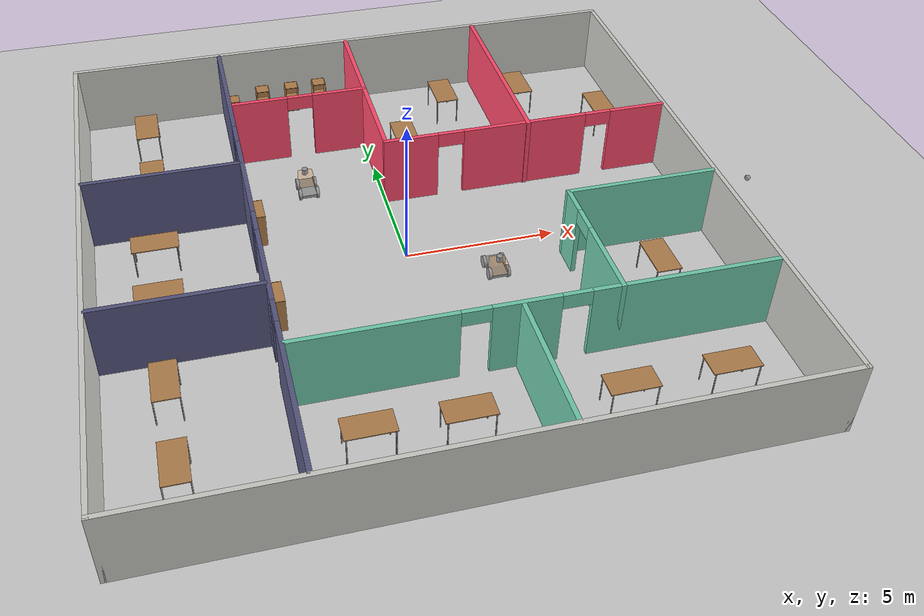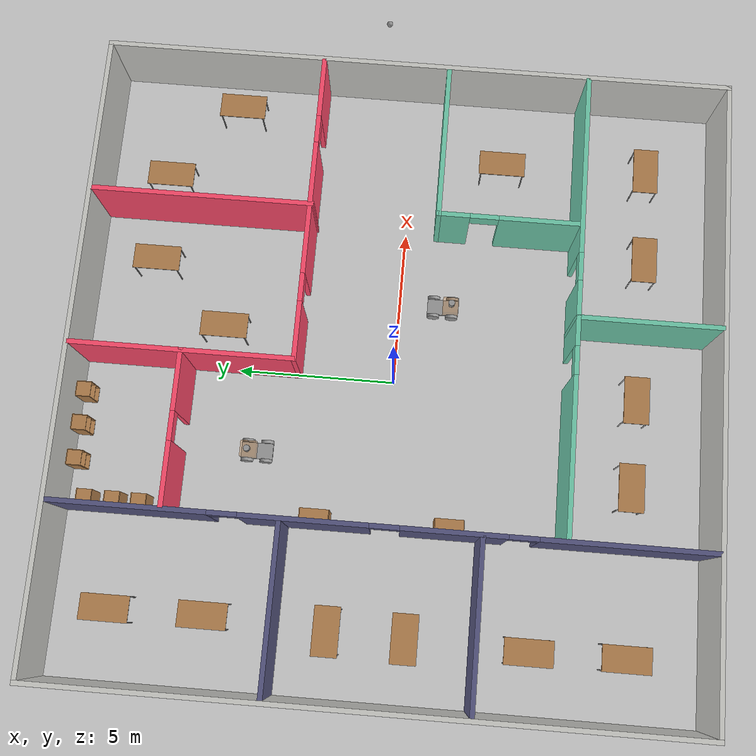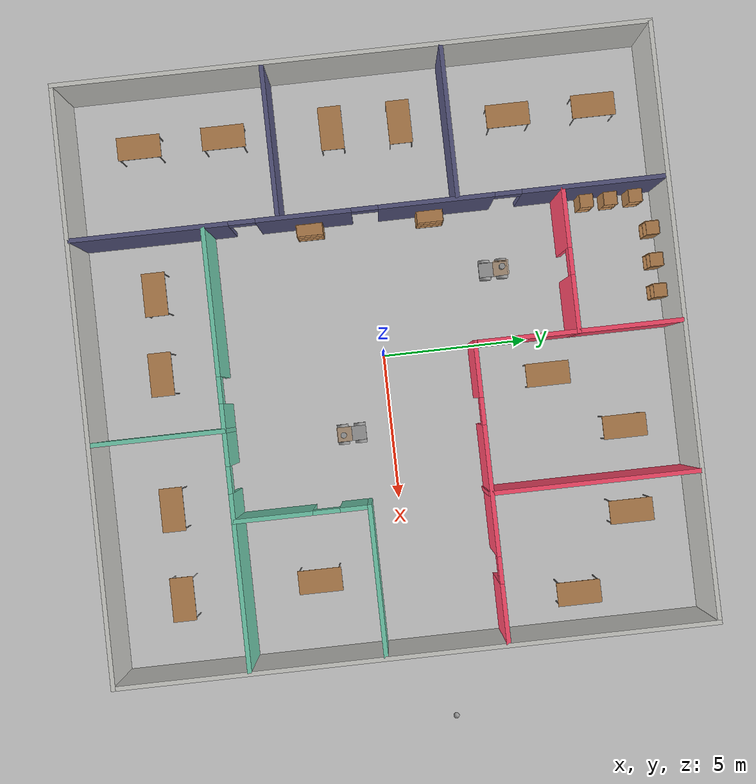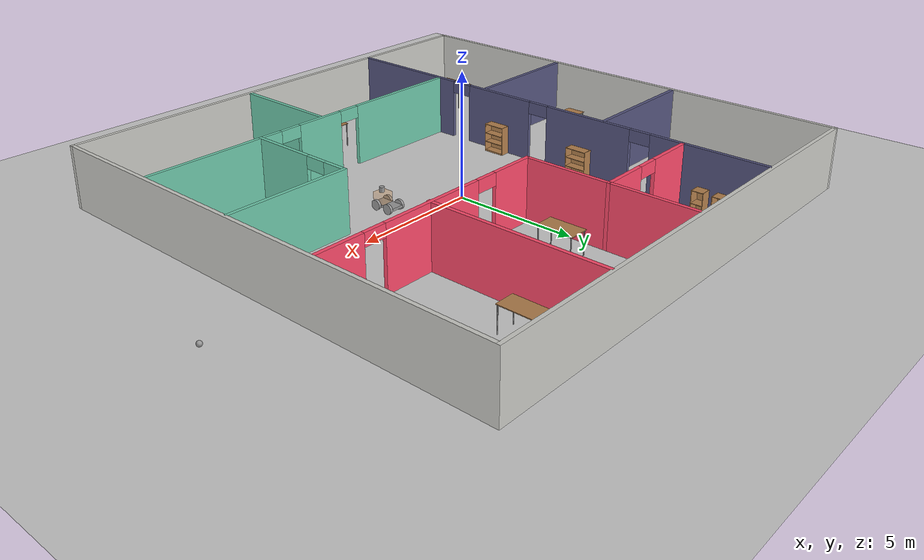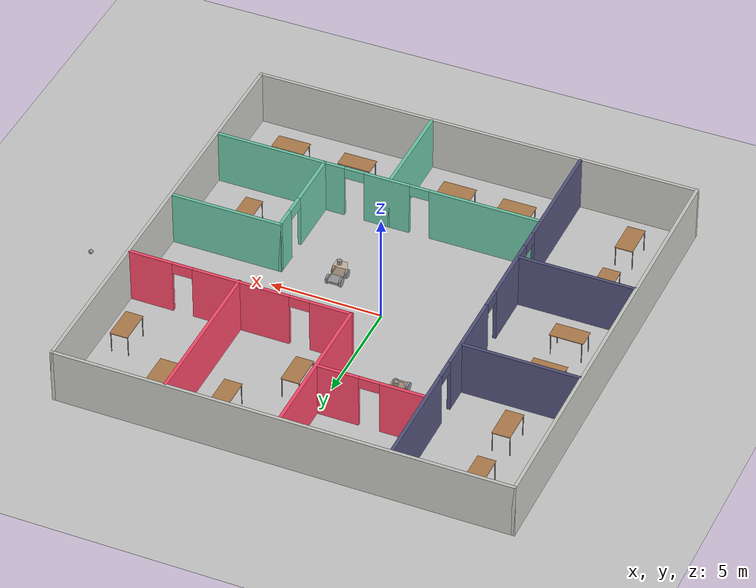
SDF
<sdf version="1.6">
 <world name="default">
  <plugin name="welcome_message" filename="libwelcome_message.so"/>
  <light name="sun" type="directional">
   <pose>0 0 10 0 -0 0</pose>
   <diffuse>0.8 0.8 0.8 1</diffuse>
   <specular>0.2 0.2 0.2 1</specular>
   <attenuation>
    <range>1000</range>
    <constant>0.9</constant>
    <linear>0.01</linear>
    <quadratic>0.001</quadratic>
   </attenuation>
   <direction>-0.5 0.1 -0.9</direction>
  </light>
  <model name="ground_plane">
   <static>1</static>
   <link name="link">
    <collision name="collision">
     <geometry><plane><normal>0 0 1</normal><size>100 100</size></plane></geometry>
     <surface>
      <contact><collide_bitmask>65535</collide_bitmask></contact>
      <friction><ode><mu>100</mu><mu2>50</mu2></ode></friction>
     </surface>
    </collision>
    <visual name="visual">
     <cast_shadows>0</cast_shadows>
     <geometry><plane><normal>0 0 1</normal><size>100 100</size></plane></geometry>
     <material>
      <script><uri>file://media/materials/scripts/gazebo.material</uri><name>Gazebo/Grey</name></script>
     </material>
    </visual>
   </link>
  </model>
  <gravity>0 0 -9.8</gravity>
  <magnetic_field>6e-06 2.3e-05 -4.2e-05</magnetic_field>
  <atmosphere type="adiabatic"/>
  <physics name="default_physics" default="0" type="ode">
   <max_step_size>0.001</max_step_size>
   <real_time_factor>1</real_time_factor>
   <real_time_update_rate>1000</real_time_update_rate>
  </physics>
  <scene><ambient>0.4 0.4 0.4 1</ambient><background>0.7 0.7 0.7 1</background><shadows>1</shadows></scene>
  <spherical_coordinates>
   <surface_model>EARTH_WGS84</surface_model>
   <latitude_deg>0</latitude_deg>
   <longitude_deg>0</longitude_deg>
   <elevation>0</elevation>
   <heading_deg>0</heading_deg>
  </spherical_coordinates>
  <model name="building">
   <link name="Wall_0">
    <collision name="Wall_0_Collision">
     <geometry><box><size>20.15 0.15 2.5</size></box></geometry>
     <pose>0 0 1.25 0 -0 0</pose>
    </collision>
    <visual name="Wall_0_Visual">
     <pose>0 0 1.25 0 -0 0</pose>
     <geometry><box><size>20.15 0.15 2.5</size></box></geometry>
     <material>
      <script><uri>file://media/materials/scripts/gazebo.material</uri><name>Gazebo/CeilingTiled</name></script>
      <ambient>1 1 1 1</ambient>
     </material>
     <meta><layer>0</layer></meta>
    </visual>
    <pose>0 -10 0 0 -0 0</pose>
   </link>
   <link name="Wall_11">
    <collision name="Wall_11_Collision">
     <geometry><box><size>4.55 0.15 2.5</size></box></geometry>
     <pose>0 0 1.25 0 -0 0</pose>
    </collision>
    <visual name="Wall_11_Visual">
     <pose>0 0 1.25 0 -0 0</pose>
     <geometry><box><size>4.55 0.15 2.5</size></box></geometry>
     <material>
      <script><uri>file://media/materials/scripts/gazebo.material</uri><name>Gazebo/Grey</name></script>
      <ambient>0.435294 0.796078 0.67451 1</ambient>
     </material>
     <meta><layer>0</layer></meta>
    </visual>
    <pose>2 -7.7 0 0 0 -1.5708</pose>
   </link>
   <link name="Wall_13">
    <pose>-2.35 6.5 0 0 -0 0</pose>
    <visual name="Wall_13_Visual_0">
     <pose>-1.42755 0 1.25 0 -0 0</pose>
     <geometry><box><size>1.99489 0.15 2.5</size></box></geometry>
     <material>
      <script><uri>file://media/materials/scripts/gazebo.material</uri><name>Gazebo/Grey</name></script>
      <ambient>1 0.290196 0.419608 1</ambient>
     </material>
     <meta><layer>0</layer></meta>
    </visual>
    <collision name="Wall_13_Collision_0">
     <geometry><box><size>1.99489 0.15 2.5</size></box></geometry>
     <pose>-1.42755 0 1.25 0 -0 0</pose>
    </collision>
    <visual name="Wall_13_Visual_1">
     <pose>1.44745 0 1.25 0 -0 0</pose>
     <geometry><box><size>1.95511 0.15 2.5</size></box></geometry>
     <material>
      <script><uri>file://media/materials/scripts/gazebo.material</uri><name>Gazebo/Grey</name></script>
      <ambient>1 0.290196 0.419608 1</ambient>
     </material>
     <meta><layer>0</layer></meta>
    </visual>
    <collision name="Wall_13_Collision_1">
     <geometry><box><size>1.95511 0.15 2.5</size></box></geometry>
     <pose>1.44745 0 1.25 0 -0 0</pose>
    </collision>
    <visual name="Wall_13_Visual_2">
     <pose>0.019894 0 2.25 0 -0 0</pose>
     <geometry><box><size>0.9 0.15 0.5</size></box></geometry>
     <material>
      <script><uri>file://media/materials/scripts/gazebo.material</uri><name>Gazebo/Grey</name></script>
      <ambient>1 0.290196 0.419608 1</ambient>
     </material>
     <meta><layer>0</layer></meta>
    </visual>
    <collision name="Wall_13_Collision_2">
     <geometry><box><size>0.9 0.15 0.5</size></box></geometry>
     <pose>0.019894 0 2.25 0 -0 0</pose>
    </collision>
   </link>
   <link name="Wall_19">
    <collision name="Wall_19_Collision">
     <geometry><box><size>7.05 0.15 2.5</size></box></geometry>
     <pose>0 0 1.25 0 -0 0</pose>
    </collision>
    <visual name="Wall_19_Visual">
     <pose>0 0 1.25 0 -0 0</pose>
     <geometry><box><size>7.05 0.15 2.5</size></box></geometry>
     <material>
      <script><uri>file://media/materials/scripts/gazebo.material</uri><name>Gazebo/Grey</name></script>
      <ambient>1 0.290196 0.419608 1</ambient>
     </material>
     <meta><layer>0</layer></meta>
    </visual>
    <pose>5 6.45 0 0 -0 1.5708</pose>
   </link>
   <link name="Wall_2">
    <collision name="Wall_2_Collision">
     <geometry><box><size>20.15 0.15 2.5</size></box></geometry>
     <pose>0 0 1.25 0 -0 0</pose>
    </collision>
    <visual name="Wall_2_Visual">
     <pose>0 0 1.25 0 -0 0</pose>
     <geometry><box><size>20.15 0.15 2.5</size></box></geometry>
     <material>
      <script><uri>file://media/materials/scripts/gazebo.material</uri><name>Gazebo/CeilingTiled</name></script>
      <ambient>1 1 1 1</ambient>
     </material>
     <meta><layer>0</layer></meta>
    </visual>
    <pose>-10 0 0 0 -0 1.5708</pose>
   </link>
   <link name="Wall_21">
    <collision name="Wall_21_Collision">
     <geometry><box><size>5.15 0.15 2.5</size></box></geometry>
     <pose>0 0 1.25 0 -0 0</pose>
    </collision>
    <visual name="Wall_21_Visual">
     <pose>0 0 1.25 0 -0 0</pose>
     <geometry><box><size>5.15 0.15 2.5</size></box></geometry>
     <material>
      <script><uri>file://media/materials/scripts/gazebo.material</uri><name>Gazebo/Grey</name></script>
      <ambient>0.333333 0.333333 0.498039 1</ambient>
     </material>
     <meta><layer>0</layer></meta>
    </visual>
    <pose>-7.4 3 0 0 -0 3.14159</pose>
   </link>
   <link name="Wall_23">
    <collision name="Wall_23_Collision">
     <geometry><box><size>6.95695 0.15 2.5</size></box></geometry>
     <pose>0 0 1.25 0 -0 0</pose>
    </collision>
    <visual name="Wall_23_Visual">
     <pose>0 0 1.25 0 -0 0</pose>
     <geometry><box><size>6.95695 0.15 2.5</size></box></geometry>
     <material>
      <script><uri>file://media/materials/scripts/gazebo.material</uri><name>Gazebo/Grey</name></script>
      <ambient>1 0.290196 0.419608 1</ambient>
     </material>
     <meta><layer>0</layer></meta>
    </visual>
    <pose>0 6.49652 0 0 -0 1.5708</pose>
   </link>
   <link name="Wall_25">
    <pose>4.95 3.04652 0 0 -0 0</pose>
    <visual name="Wall_25_Visual_0">
     <pose>-4.07462 0 1.25 0 -0 0</pose>
     <geometry><box><size>1.90076 0.15 2.5</size></box></geometry>
     <material>
      <script><uri>file://media/materials/scripts/gazebo.material</uri><name>Gazebo/Grey</name></script>
      <ambient>1 0.290196 0.419608 1</ambient>
     </material>
     <meta><layer>0</layer></meta>
    </visual>
    <collision name="Wall_25_Collision_0">
     <geometry><box><size>1.90076 0.15 2.5</size></box></geometry>
     <pose>-4.07462 0 1.25 0 -0 0</pose>
    </collision>
    <visual name="Wall_25_Visual_1">
     <pose>-0.045637 0 1.25 0 -0 0</pose>
     <geometry><box><size>4.3572 0.15 2.5</size></box></geometry>
     <material>
      <script><uri>file://media/materials/scripts/gazebo.material</uri><name>Gazebo/Grey</name></script>
      <ambient>1 0.290196 0.419608 1</ambient>
     </material>
     <meta><layer>0</layer></meta>
    </visual>
    <collision name="Wall_25_Collision_1">
     <geometry><box><size>4.3572 0.15 2.5</size></box></geometry>
     <pose>-0.045637 0 1.25 0 -0 0</pose>
    </collision>
    <visual name="Wall_25_Visual_2">
     <pose>4.02898 0 1.25 0 -0 0</pose>
     <geometry><box><size>1.99204 0.15 2.5</size></box></geometry>
     <material>
      <script><uri>file://media/materials/scripts/gazebo.material</uri><name>Gazebo/Grey</name></script>
      <ambient>1 0.290196 0.419608 1</ambient>
     </material>
     <meta><layer>0</layer></meta>
    </visual>
    <collision name="Wall_25_Collision_2">
     <geometry><box><size>1.99204 0.15 2.5</size></box></geometry>
     <pose>4.02898 0 1.25 0 -0 0</pose>
    </collision>
    <visual name="Wall_25_Visual_3">
     <pose>-2.67424 0 2.25 0 -0 0</pose>
     <geometry><box><size>0.9 0.15 0.5</size></box></geometry>
     <material>
      <script><uri>file://media/materials/scripts/gazebo.material</uri><name>Gazebo/Grey</name></script>
      <ambient>1 0.290196 0.419608 1</ambient>
     </material>
     <meta><layer>0</layer></meta>
    </visual>
    <collision name="Wall_25_Collision_3">
     <geometry><box><size>0.9 0.15 0.5</size></box></geometry>
     <pose>-2.67424 0 2.25 0 -0 0</pose>
    </collision>
    <visual name="Wall_25_Visual_4">
     <pose>2.58296 0 2.25 0 -0 0</pose>
     <geometry><box><size>0.9 0.15 0.5</size></box></geometry>
     <material>
      <script><uri>file://media/materials/scripts/gazebo.material</uri><name>Gazebo/Grey</name></script>
      <ambient>1 0.290196 0.419608 1</ambient>
     </material>
     <meta><layer>0</layer></meta>
    </visual>
    <collision name="Wall_25_Collision_4">
     <geometry><box><size>0.9 0.15 0.5</size></box></geometry>
     <pose>2.58296 0 2.25 0 -0 0</pose>
    </collision>
   </link>
   <link name="Wall_27">
    <pose>5 -3.25 0 0 0 -1.5708</pose>
    <visual name="Wall_27_Visual_0">
     <pose>-1.79644 0 1.25 0 -0 0</pose>
     <geometry><box><size>1.05711 0.15 2.5</size></box></geometry>
     <material>
      <script><uri>file://media/materials/scripts/gazebo.material</uri><name>Gazebo/Grey</name></script>
      <ambient>0.435294 0.796078 0.67451 1</ambient>
     </material>
     <meta><layer>0</layer></meta>
    </visual>
    <collision name="Wall_27_Collision_0">
     <geometry><box><size>1.05711 0.15 2.5</size></box></geometry>
     <pose>-1.79644 0 1.25 0 -0 0</pose>
    </collision>
    <visual name="Wall_27_Visual_1">
     <pose>0.978556 0 1.25 0 -0 0</pose>
     <geometry><box><size>2.69289 0.15 2.5</size></box></geometry>
     <material>
      <script><uri>file://media/materials/scripts/gazebo.material</uri><name>Gazebo/Grey</name></script>
      <ambient>0.435294 0.796078 0.67451 1</ambient>
     </material>
     <meta><layer>0</layer></meta>
    </visual>
    <collision name="Wall_27_Collision_1">
     <geometry><box><size>2.69289 0.15 2.5</size></box></geometry>
     <pose>0.978556 0 1.25 0 -0 0</pose>
    </collision>
    <visual name="Wall_27_Visual_2">
     <pose>-0.817888 0 2.25 0 -0 0</pose>
     <geometry><box><size>0.9 0.15 0.5</size></box></geometry>
     <material>
      <script><uri>file://media/materials/scripts/gazebo.material</uri><name>Gazebo/Grey</name></script>
      <ambient>0.435294 0.796078 0.67451 1</ambient>
     </material>
     <meta><layer>0</layer></meta>
    </visual>
    <collision name="Wall_27_Collision_2">
     <geometry><box><size>0.9 0.15 0.5</size></box></geometry>
     <pose>-0.817888 0 2.25 0 -0 0</pose>
    </collision>
   </link>
   <link name="Wall_29">
    <collision name="Wall_29_Collision">
     <geometry><box><size>5.05 0.15 2.5</size></box></geometry>
     <pose>0 0 1.25 0 -0 0</pose>
    </collision>
    <visual name="Wall_29_Visual">
     <pose>0 0 1.25 0 -0 0</pose>
     <geometry><box><size>5.05 0.15 2.5</size></box></geometry>
     <material>
      <script><uri>file://media/materials/scripts/gazebo.material</uri><name>Gazebo/Grey</name></script>
      <ambient>0.435294 0.796078 0.67451 1</ambient>
     </material>
     <meta><layer>0</layer></meta>
    </visual>
    <pose>7.45 -1 0 0 -0 0</pose>
   </link>
   <link name="Wall_3">
    <collision name="Wall_3_Collision">
     <geometry><box><size>20.15 0.15 2.5</size></box></geometry>
     <pose>0 0 1.25 0 -0 0</pose>
    </collision>
    <visual name="Wall_3_Visual">
     <pose>0 0 1.25 0 -0 0</pose>
     <geometry><box><size>20.15 0.15 2.5</size></box></geometry>
     <material>
      <script><uri>file://media/materials/scripts/gazebo.material</uri><name>Gazebo/CeilingTiled</name></script>
      <ambient>1 1 1 1</ambient>
     </material>
     <meta><layer>0</layer></meta>
    </visual>
    <pose>0 10 0 0 -0 0</pose>
   </link>
   <link name="Wall_31">
    <collision name="Wall_31_Collision">
     <geometry><box><size>5.15 0.15 2.5</size></box></geometry>
     <pose>0 0 1.25 0 -0 0</pose>
    </collision>
    <visual name="Wall_31_Visual">
     <pose>0 0 1.25 0 -0 0</pose>
     <geometry><box><size>5.15 0.15 2.5</size></box></geometry>
     <material>
      <script><uri>file://media/materials/scripts/gazebo.material</uri><name>Gazebo/Grey</name></script>
      <ambient>0.333333 0.333333 0.498039 1</ambient>
     </material>
     <meta><layer>0</layer></meta>
    </visual>
    <pose>-7.4 -3 0 0 -0 3.14159</pose>
   </link>
   <link name="Wall_4">
    <collision name="Wall_4_Collision">
     <geometry><box><size>20.15 0.15 2.5</size></box></geometry>
     <pose>0 0 1.25 0 -0 0</pose>
    </collision>
    <visual name="Wall_4_Visual">
     <pose>0 0 1.25 0 -0 0</pose>
     <geometry><box><size>20.15 0.15 2.5</size></box></geometry>
     <material>
      <script><uri>file://media/materials/scripts/gazebo.material</uri><name>Gazebo/CeilingTiled</name></script>
      <ambient>1 1 1 1</ambient>
     </material>
     <meta><layer>0</layer></meta>
    </visual>
    <pose>10 0 0 0 0 -1.5708</pose>
   </link>
   <link name="Wall_6">
    <pose>-4.8 0 0 0 -0 1.5708</pose>
    <visual name="Wall_6_Visual_0">
     <pose>-7.31251 0 1.25 0 -0 0</pose>
     <geometry><box><size>5.32498 0.15 2.5</size></box></geometry>
     <material>
      <script><uri>file://media/materials/scripts/gazebo.material</uri><name>Gazebo/Grey</name></script>
      <ambient>0.333333 0.333333 0.498039 1</ambient>
     </material>
     <meta><layer>0</layer></meta>
    </visual>
    <collision name="Wall_6_Collision_0">
     <geometry><box><size>5.32498 0.15 2.5</size></box></geometry>
     <pose>-7.31251 0 1.25 0 -0 0</pose>
    </collision>
    <visual name="Wall_6_Visual_1">
     <pose>-2.15297 0 1.25 0 -0 0</pose>
     <geometry><box><size>3.1941 0.15 2.5</size></box></geometry>
     <material>
      <script><uri>file://media/materials/scripts/gazebo.material</uri><name>Gazebo/Grey</name></script>
      <ambient>0.333333 0.333333 0.498039 1</ambient>
     </material>
     <meta><layer>0</layer></meta>
    </visual>
    <collision name="Wall_6_Collision_1">
     <geometry><box><size>3.1941 0.15 2.5</size></box></geometry>
     <pose>-2.15297 0 1.25 0 -0 0</pose>
    </collision>
    <visual name="Wall_6_Visual_2">
     <pose>2.29006 0 1.25 0 -0 0</pose>
     <geometry><box><size>3.89196 0.15 2.5</size></box></geometry>
     <material>
      <script><uri>file://media/materials/scripts/gazebo.material</uri><name>Gazebo/Grey</name></script>
      <ambient>0.333333 0.333333 0.498039 1</ambient>
     </material>
     <meta><layer>0</layer></meta>
    </visual>
    <collision name="Wall_6_Collision_2">
     <geometry><box><size>3.89196 0.15 2.5</size></box></geometry>
     <pose>2.29006 0 1.25 0 -0 0</pose>
    </collision>
    <visual name="Wall_6_Visual_3">
     <pose>7.55552 0 1.25 0 -0 0</pose>
     <geometry><box><size>4.83895 0.15 2.5</size></box></geometry>
     <material>
      <script><uri>file://media/materials/scripts/gazebo.material</uri><name>Gazebo/Grey</name></script>
      <ambient>0.333333 0.333333 0.498039 1</ambient>
     </material>
     <meta><layer>0</layer></meta>
    </visual>
    <collision name="Wall_6_Collision_3">
     <geometry><box><size>4.83895 0.15 2.5</size></box></geometry>
     <pose>7.55552 0 1.25 0 -0 0</pose>
    </collision>
    <visual name="Wall_6_Visual_4">
     <pose>-4.20002 0 2.25 0 -0 0</pose>
     <geometry><box><size>0.9 0.15 0.5</size></box></geometry>
     <material>
      <script><uri>file://media/materials/scripts/gazebo.material</uri><name>Gazebo/Grey</name></script>
      <ambient>0.333333 0.333333 0.498039 1</ambient>
     </material>
     <meta><layer>0</layer></meta>
    </visual>
    <collision name="Wall_6_Collision_4">
     <geometry><box><size>0.9 0.15 0.5</size></box></geometry>
     <pose>-4.20002 0 2.25 0 -0 0</pose>
    </collision>
    <visual name="Wall_6_Visual_5">
     <pose>-0.105917 0 2.25 0 -0 0</pose>
     <geometry><box><size>0.9 0.15 0.5</size></box></geometry>
     <material>
      <script><uri>file://media/materials/scripts/gazebo.material</uri><name>Gazebo/Grey</name></script>
      <ambient>0.333333 0.333333 0.498039 1</ambient>
     </material>
     <meta><layer>0</layer></meta>
    </visual>
    <collision name="Wall_6_Collision_5">
     <geometry><box><size>0.9 0.15 0.5</size></box></geometry>
     <pose>-0.105917 0 2.25 0 -0 0</pose>
    </collision>
    <visual name="Wall_6_Visual_6">
     <pose>4.68605 0 2.25 0 -0 0</pose>
     <geometry><box><size>0.9 0.15 0.5</size></box></geometry>
     <material>
      <script><uri>file://media/materials/scripts/gazebo.material</uri><name>Gazebo/Grey</name></script>
      <ambient>0.333333 0.333333 0.498039 1</ambient>
     </material>
     <meta><layer>0</layer></meta>
    </visual>
    <collision name="Wall_6_Collision_6">
     <geometry><box><size>0.9 0.15 0.5</size></box></geometry>
     <pose>4.68605 0 2.25 0 -0 0</pose>
    </collision>
   </link>
   <link name="Wall_8">
    <pose>2.6 -5.5 0 0 -0 0</pose>
    <visual name="Wall_8_Visual_0">
     <pose>-4.88879 0 1.25 0 -0 0</pose>
     <geometry><box><size>4.97243 0.15 2.5</size></box></geometry>
     <material>
      <script><uri>file://media/materials/scripts/gazebo.material</uri><name>Gazebo/Grey</name></script>
      <ambient>0.435294 0.796078 0.67451 1</ambient>
     </material>
     <meta><layer>0</layer></meta>
    </visual>
    <collision name="Wall_8_Collision_0">
     <geometry><box><size>4.97243 0.15 2.5</size></box></geometry>
     <pose>-4.88879 0 1.25 0 -0 0</pose>
    </collision>
    <visual name="Wall_8_Visual_1">
     <pose>-0.46381 0 1.25 0 -0 0</pose>
     <geometry><box><size>2.07753 0.15 2.5</size></box></geometry>
     <material>
      <script><uri>file://media/materials/scripts/gazebo.material</uri><name>Gazebo/Grey</name></script>
      <ambient>0.435294 0.796078 0.67451 1</ambient>
     </material>
     <meta><layer>0</layer></meta>
    </visual>
    <collision name="Wall_8_Collision_1">
     <geometry><box><size>2.07753 0.15 2.5</size></box></geometry>
     <pose>-0.46381 0 1.25 0 -0 0</pose>
    </collision>
    <visual name="Wall_8_Visual_2">
     <pose>4.42498 0 1.25 0 -0 0</pose>
     <geometry><box><size>5.90005 0.15 2.5</size></box></geometry>
     <material>
      <script><uri>file://media/materials/scripts/gazebo.material</uri><name>Gazebo/Grey</name></script>
      <ambient>0.435294 0.796078 0.67451 1</ambient>
     </material>
     <meta><layer>0</layer></meta>
    </visual>
    <collision name="Wall_8_Collision_2">
     <geometry><box><size>5.90005 0.15 2.5</size></box></geometry>
     <pose>4.42498 0 1.25 0 -0 0</pose>
    </collision>
    <visual name="Wall_8_Visual_3">
     <pose>-1.95257 0 2.25 0 -0 0</pose>
     <geometry><box><size>0.9 0.15 0.5</size></box></geometry>
     <material>
      <script><uri>file://media/materials/scripts/gazebo.material</uri><name>Gazebo/Grey</name></script>
      <ambient>0.435294 0.796078 0.67451 1</ambient>
     </material>
     <meta><layer>0</layer></meta>
    </visual>
    <collision name="Wall_8_Collision_3">
     <geometry><box><size>0.9 0.15 0.5</size></box></geometry>
     <pose>-1.95257 0 2.25 0 -0 0</pose>
    </collision>
    <visual name="Wall_8_Visual_4">
     <pose>1.02496 0 2.25 0 -0 0</pose>
     <geometry><box><size>0.9 0.15 0.5</size></box></geometry>
     <material>
      <script><uri>file://media/materials/scripts/gazebo.material</uri><name>Gazebo/Grey</name></script>
      <ambient>0.435294 0.796078 0.67451 1</ambient>
     </material>
     <meta><layer>0</layer></meta>
    </visual>
    <collision name="Wall_8_Collision_4">
     <geometry><box><size>0.9 0.15 0.5</size></box></geometry>
     <pose>1.02496 0 2.25 0 -0 0</pose>
    </collision>
   </link>
   <static>1</static>
  </model>
  <model name="bookshelf">
   <static>1</static>
   <link name="link">
    <inertial><mass>1</mass></inertial>
    <collision name="back">
     <pose>0 0.005 0.6 0 -0 0</pose>
     <geometry><box><size>0.9 0.01 1.2</size></box></geometry>
    </collision>
    <visual name="visual1">
     <pose>0 0.005 0.6 0 -0 0</pose>
     <geometry><box><size>0.9 0.01 1.2</size></box></geometry>
     <material>
      <script><uri>file://media/materials/scripts/gazebo.material</uri><name>Gazebo/Wood</name></script>
     </material>
    </visual>
    <collision name="left_side">
     <pose>0.45 -0.195 0.6 0 -0 0</pose>
     <geometry><box><size>0.02 0.4 1.2</size></box></geometry>
    </collision>
    <visual name="visual2">
     <pose>0.45 -0.195 0.6 0 -0 0</pose>
     <geometry><box><size>0.02 0.4 1.2</size></box></geometry>
     <material>
      <script><uri>file://media/materials/scripts/gazebo.material</uri><name>Gazebo/Wood</name></script>
     </material>
    </visual>
    <collision name="right_side">
     <pose>-0.45 -0.195 0.6 0 -0 0</pose>
     <geometry><box><size>0.02 0.4 1.2</size></box></geometry>
    </collision>
    <visual name="visual3">
     <pose>-0.45 -0.195 0.6 0 -0 0</pose>
     <geometry><box><size>0.02 0.4 1.2</size></box></geometry>
     <material>
      <script><uri>file://media/materials/scripts/gazebo.material</uri><name>Gazebo/Wood</name></script>
     </material>
    </visual>
    <collision name="bottom">
     <pose>0 -0.195 0.03 0 -0 0</pose>
     <geometry><box><size>0.88 0.4 0.06</size></box></geometry>
    </collision>
    <visual name="visual4">
     <pose>0 -0.195 0.03 0 -0 0</pose>
     <geometry><box><size>0.88 0.4 0.06</size></box></geometry>
     <material>
      <script><uri>file://media/materials/scripts/gazebo.material</uri><name>Gazebo/Wood</name></script>
     </material>
    </visual>
    <collision name="top">
     <pose>0 -0.195 1.19 0 -0 0</pose>
     <geometry><box><size>0.88 0.4 0.02</size></box></geometry>
    </collision>
    <visual name="visual5">
     <pose>0 -0.195 1.19 0 -0 0</pose>
     <geometry><box><size>0.88 0.4 0.02</size></box></geometry>
     <material>
      <script><uri>file://media/materials/scripts/gazebo.material</uri><name>Gazebo/Wood</name></script>
     </material>
    </visual>
    <collision name="low_shelf">
     <pose>0 -0.195 0.43 0 -0 0</pose>
     <geometry><box><size>0.88 0.4 0.02</size></box></geometry>
    </collision>
    <visual name="visual6">
     <pose>0 -0.195 0.43 0 -0 0</pose>
     <geometry><box><size>0.88 0.4 0.02</size></box></geometry>
     <material>
      <script><uri>file://media/materials/scripts/gazebo.material</uri><name>Gazebo/Wood</name></script>
     </material>
    </visual>
    <collision name="high_shelf">
     <pose>0 -0.195 0.8 0 -0 0</pose>
     <geometry><box><size>0.88 0.4 0.02</size></box></geometry>
    </collision>
    <visual name="visual7">
     <pose>0 -0.195 0.8 0 -0 0</pose>
     <geometry><box><size>0.88 0.4 0.02</size></box></geometry>
     <material>
      <script><uri>file://media/materials/scripts/gazebo.material</uri><name>Gazebo/Wood</name></script>
     </material>
    </visual>
   </link>
   <pose>-4.70667 -2.04836 0 0 -0 1.5707</pose>
  </model>
  <model name="cabinet">
   <static>1</static>
   <link name="cabinet_bottom_plate">
    <inertial>
     <pose>0 0 -1 0 -0 0</pose>
     <inertia><ixx>2.05</ixx><ixy>0</ixy><ixz>0</ixz><iyy>2.05</iyy><iyz>0</iyz><izz>2.05</izz></inertia>
     <mass>25</mass>
    </inertial>
    <collision name="cabinet_bottom_plate_geom">
     <pose>0 0 0.01 0 -0 0</pose>
     <geometry><box><size>0.45 0.45 0.02</size></box></geometry>
    </collision>
    <visual name="cabinet_bottom_plate_geom_visual">
     <pose>0 0 0.01 0 -0 0</pose>
     <geometry><box><size>0.45 0.45 0.02</size></box></geometry>
     <material>
      <script><uri>file://media/materials/scripts/gazebo.material</uri><name>Gazebo/Wood</name></script>
     </material>
    </visual>
    <collision name="cabinet_bottom_plate_geom_cabinet_back_plate">
     <pose>0.235 0 0.51 0 -0 0</pose>
     <geometry><box><size>0.02 0.45 1.02</size></box></geometry>
    </collision>
    <visual name="cabinet_bottom_plate_geom_cabinet_back_plate_visual">
     <pose>0.235 0 0.51 0 -0 0</pose>
     <geometry><box><size>0.02 0.45 1.02</size></box></geometry>
     <material>
      <script><uri>file://media/materials/scripts/gazebo.material</uri><name>Gazebo/Wood</name></script>
     </material>
    </visual>
    <collision name="cabinet_bottom_plate_geom_cabinet_left_plate">
     <pose>0 0.235 0.51 0 -0 0</pose>
     <geometry><box><size>0.45 0.02 1.02</size></box></geometry>
    </collision>
    <visual name="cabinet_bottom_plate_geom_cabinet_left_plate_visual">
     <pose>0 0.235 0.51 0 -0 0</pose>
     <geometry><box><size>0.45 0.02 1.02</size></box></geometry>
     <material>
      <script><uri>file://media/materials/scripts/gazebo.material</uri><name>Gazebo/Wood</name></script>
     </material>
    </visual>
    <collision name="cabinet_bottom_plate_geom_cabinet_middle_plate">
     <pose>0 0 0.51 0 -0 0</pose>
     <geometry><box><size>0.45 0.45 0.02</size></box></geometry>
    </collision>
    <visual name="cabinet_bottom_plate_geom_cabinet_middle_plate_visual">
     <pose>0 0 0.51 0 -0 0</pose>
     <geometry><box><size>0.45 0.45 0.02</size></box></geometry>
     <material>
      <script><uri>file://media/materials/scripts/gazebo.material</uri><name>Gazebo/Wood</name></script>
     </material>
    </visual>
    <collision name="cabinet_bottom_plate_geom_cabinet_right_plate">
     <pose>0 -0.235 0.51 0 -0 0</pose>
     <geometry><box><size>0.45 0.02 1.02</size></box></geometry>
    </collision>
    <visual name="cabinet_bottom_plate_geom_cabinet_right_plate_visual">
     <pose>0 -0.235 0.51 0 -0 0</pose>
     <geometry><box><size>0.45 0.02 1.02</size></box></geometry>
     <material>
      <script><uri>file://media/materials/scripts/gazebo.material</uri><name>Gazebo/Wood</name></script>
     </material>
    </visual>
    <collision name="cabinet_bottom_plate_geom_cabinet_top_plate">
     <pose>0 0 1.01 0 -0 0</pose>
     <geometry><box><size>0.45 0.45 0.02</size></box></geometry>
    </collision>
    <visual name="cabinet_bottom_plate_geom_cabinet_top_plate_visual">
     <pose>0 0 1.01 0 -0 0</pose>
     <geometry><box><size>0.45 0.45 0.02</size></box></geometry>
     <material>
      <script><uri>file://media/materials/scripts/gazebo.material</uri><name>Gazebo/Wood</name></script>
     </material>
    </visual>
   </link>
   <pose>-4.49605 9.20323 0 0 0 -3.13728</pose>
  </model>
  <model name="table">
   <static>1</static>
   <link name="link">
    <collision name="surface">
     <pose>0 0 1 0 -0 0</pose>
     <geometry><box><size>1.5 0.8 0.03</size></box></geometry>
     <surface><friction><ode><mu>0.6</mu><mu2>0.6</mu2></ode></friction></surface>
    </collision>
    <visual name="visual1">
     <pose>0 0 1 0 -0 0</pose>
     <geometry><box><size>1.5 0.8 0.03</size></box></geometry>
     <material>
      <script><uri>file://media/materials/scripts/gazebo.material</uri><name>Gazebo/Wood</name></script>
     </material>
    </visual>
    <collision name="front_left_leg">
     <pose>0.68 0.38 0.5 0 -0 0</pose>
     <geometry><cylinder><radius>0.02</radius><length>1</length></cylinder></geometry>
    </collision>
    <visual name="front_left_leg">
     <pose>0.68 0.38 0.5 0 -0 0</pose>
     <geometry><cylinder><radius>0.02</radius><length>1</length></cylinder></geometry>
     <material>
      <script><uri>file://media/materials/scripts/gazebo.material</uri><name>Gazebo/Grey</name></script>
     </material>
    </visual>
    <collision name="front_right_leg">
     <pose>0.68 -0.38 0.5 0 -0 0</pose>
     <geometry><cylinder><radius>0.02</radius><length>1</length></cylinder></geometry>
    </collision>
    <visual name="front_right_leg">
     <pose>0.68 -0.38 0.5 0 -0 0</pose>
     <geometry><cylinder><radius>0.02</radius><length>1</length></cylinder></geometry>
     <material>
      <script><uri>file://media/materials/scripts/gazebo.material</uri><name>Gazebo/Grey</name></script>
     </material>
    </visual>
    <collision name="back_right_leg">
     <pose>-0.68 -0.38 0.5 0 -0 0</pose>
     <geometry><cylinder><radius>0.02</radius><length>1</length></cylinder></geometry>
    </collision>
    <visual name="back_right_leg">
     <pose>-0.68 -0.38 0.5 0 -0 0</pose>
     <geometry><cylinder><radius>0.02</radius><length>1</length></cylinder></geometry>
     <material>
      <script><uri>file://media/materials/scripts/gazebo.material</uri><name>Gazebo/Grey</name></script>
     </material>
    </visual>
    <collision name="back_left_leg">
     <pose>-0.68 0.38 0.5 0 -0 0</pose>
     <geometry><cylinder><radius>0.02</radius><length>1</length></cylinder></geometry>
    </collision>
    <visual name="back_left_leg">
     <pose>-0.68 0.38 0.5 0 -0 0</pose>
     <geometry><cylinder><radius>0.02</radius><length>1</length></cylinder></geometry>
     <material>
      <script><uri>file://media/materials/scripts/gazebo.material</uri><name>Gazebo/Grey</name></script>
     </material>
    </visual>
   </link>
   <pose>-2.89831 -7.57702 0 0 -0 0</pose>
  </model>
  <model name="table_clone">
   <static>1</static>
   <link name="link">
    <collision name="surface">
     <pose>0 0 1 0 -0 0</pose>
     <geometry><box><size>1.5 0.8 0.03</size></box></geometry>
     <surface><friction><ode><mu>0.6</mu><mu2>0.6</mu2></ode></friction></surface>
    </collision>
    <visual name="visual1">
     <pose>0 0 1 0 -0 0</pose>
     <geometry><box><size>1.5 0.8 0.03</size></box></geometry>
     <material>
      <script><uri>file://media/materials/scripts/gazebo.material</uri><name>Gazebo/Wood</name></script>
     </material>
    </visual>
    <collision name="front_left_leg">
     <pose>0.68 0.38 0.5 0 -0 0</pose>
     <geometry><cylinder><radius>0.02</radius><length>1</length></cylinder></geometry>
    </collision>
    <visual name="front_left_leg">
     <pose>0.68 0.38 0.5 0 -0 0</pose>
     <geometry><cylinder><radius>0.02</radius><length>1</length></cylinder></geometry>
     <material>
      <script><uri>file://media/materials/scripts/gazebo.material</uri><name>Gazebo/Grey</name></script>
     </material>
    </visual>
    <collision name="front_right_leg">
     <pose>0.68 -0.38 0.5 0 -0 0</pose>
     <geometry><cylinder><radius>0.02</radius><length>1</length></cylinder></geometry>
    </collision>
    <visual name="front_right_leg">
     <pose>0.68 -0.38 0.5 0 -0 0</pose>
     <geometry><cylinder><radius>0.02</radius><length>1</length></cylinder></geometry>
     <material>
      <script><uri>file://media/materials/scripts/gazebo.material</uri><name>Gazebo/Grey</name></script>
     </material>
    </visual>
    <collision name="back_right_leg">
     <pose>-0.68 -0.38 0.5 0 -0 0</pose>
     <geometry><cylinder><radius>0.02</radius><length>1</length></cylinder></geometry>
    </collision>
    <visual name="back_right_leg">
     <pose>-0.68 -0.38 0.5 0 -0 0</pose>
     <geometry><cylinder><radius>0.02</radius><length>1</length></cylinder></geometry>
     <material>
      <script><uri>file://media/materials/scripts/gazebo.material</uri><name>Gazebo/Grey</name></script>
     </material>
    </visual>
    <collision name="back_left_leg">
     <pose>-0.68 0.38 0.5 0 -0 0</pose>
     <geometry><cylinder><radius>0.02</radius><length>1</length></cylinder></geometry>
    </collision>
    <visual name="back_left_leg">
     <pose>-0.68 0.38 0.5 0 -0 0</pose>
     <geometry><cylinder><radius>0.02</radius><length>1</length></cylinder></geometry>
     <material>
      <script><uri>file://media/materials/scripts/gazebo.material</uri><name>Gazebo/Grey</name></script>
     </material>
    </visual>
   </link>
   <pose>-0.143006 -7.64818 0 0 -0 0</pose>
  </model>
  <model name="table_clone_0">
   <static>1</static>
   <link name="link">
    <collision name="surface">
     <pose>0 0 1 0 -0 0</pose>
     <geometry><box><size>1.5 0.8 0.03</size></box></geometry>
     <surface><friction><ode><mu>0.6</mu><mu2>0.6</mu2></ode></friction></surface>
    </collision>
    <visual name="visual1">
     <pose>0 0 1 0 -0 0</pose>
     <geometry><box><size>1.5 0.8 0.03</size></box></geometry>
     <material>
      <script><uri>file://media/materials/scripts/gazebo.material</uri><name>Gazebo/Wood</name></script>
     </material>
    </visual>
    <collision name="front_left_leg">
     <pose>0.68 0.38 0.5 0 -0 0</pose>
     <geometry><cylinder><radius>0.02</radius><length>1</length></cylinder></geometry>
    </collision>
    <visual name="front_left_leg">
     <pose>0.68 0.38 0.5 0 -0 0</pose>
     <geometry><cylinder><radius>0.02</radius><length>1</length></cylinder></geometry>
     <material>
      <script><uri>file://media/materials/scripts/gazebo.material</uri><name>Gazebo/Grey</name></script>
     </material>
    </visual>
    <collision name="front_right_leg">
     <pose>0.68 -0.38 0.5 0 -0 0</pose>
     <geometry><cylinder><radius>0.02</radius><length>1</length></cylinder></geometry>
    </collision>
    <visual name="front_right_leg">
     <pose>0.68 -0.38 0.5 0 -0 0</pose>
     <geometry><cylinder><radius>0.02</radius><length>1</length></cylinder></geometry>
     <material>
      <script><uri>file://media/materials/scripts/gazebo.material</uri><name>Gazebo/Grey</name></script>
     </material>
    </visual>
    <collision name="back_right_leg">
     <pose>-0.68 -0.38 0.5 0 -0 0</pose>
     <geometry><cylinder><radius>0.02</radius><length>1</length></cylinder></geometry>
    </collision>
    <visual name="back_right_leg">
     <pose>-0.68 -0.38 0.5 0 -0 0</pose>
     <geometry><cylinder><radius>0.02</radius><length>1</length></cylinder></geometry>
     <material>
      <script><uri>file://media/materials/scripts/gazebo.material</uri><name>Gazebo/Grey</name></script>
     </material>
    </visual>
    <collision name="back_left_leg">
     <pose>-0.68 0.38 0.5 0 -0 0</pose>
     <geometry><cylinder><radius>0.02</radius><length>1</length></cylinder></geometry>
    </collision>
    <visual name="back_left_leg">
     <pose>-0.68 0.38 0.5 0 -0 0</pose>
     <geometry><cylinder><radius>0.02</radius><length>1</length></cylinder></geometry>
     <material>
      <script><uri>file://media/materials/scripts/gazebo.material</uri><name>Gazebo/Grey</name></script>
     </material>
    </visual>
   </link>
   <pose>4.49827 -7.74923 0 0 -0 0</pose>
  </model>
  <model name="table_clone_1">
   <static>1</static>
   <link name="link">
    <collision name="surface">
     <pose>0 0 1 0 -0 0</pose>
     <geometry><box><size>1.5 0.8 0.03</size></box></geometry>
     <surface><friction><ode><mu>0.6</mu><mu2>0.6</mu2></ode></friction></surface>
    </collision>
    <visual name="visual1">
     <pose>0 0 1 0 -0 0</pose>
     <geometry><box><size>1.5 0.8 0.03</size></box></geometry>
     <material>
      <script><uri>file://media/materials/scripts/gazebo.material</uri><name>Gazebo/Wood</name></script>
     </material>
    </visual>
    <collision name="front_left_leg">
     <pose>0.68 0.38 0.5 0 -0 0</pose>
     <geometry><cylinder><radius>0.02</radius><length>1</length></cylinder></geometry>
    </collision>
    <visual name="front_left_leg">
     <pose>0.68 0.38 0.5 0 -0 0</pose>
     <geometry><cylinder><radius>0.02</radius><length>1</length></cylinder></geometry>
     <material>
      <script><uri>file://media/materials/scripts/gazebo.material</uri><name>Gazebo/Grey</name></script>
     </material>
    </visual>
    <collision name="front_right_leg">
     <pose>0.68 -0.38 0.5 0 -0 0</pose>
     <geometry><cylinder><radius>0.02</radius><length>1</length></cylinder></geometry>
    </collision>
    <visual name="front_right_leg">
     <pose>0.68 -0.38 0.5 0 -0 0</pose>
     <geometry><cylinder><radius>0.02</radius><length>1</length></cylinder></geometry>
     <material>
      <script><uri>file://media/materials/scripts/gazebo.material</uri><name>Gazebo/Grey</name></script>
     </material>
    </visual>
    <collision name="back_right_leg">
     <pose>-0.68 -0.38 0.5 0 -0 0</pose>
     <geometry><cylinder><radius>0.02</radius><length>1</length></cylinder></geometry>
    </collision>
    <visual name="back_right_leg">
     <pose>-0.68 -0.38 0.5 0 -0 0</pose>
     <geometry><cylinder><radius>0.02</radius><length>1</length></cylinder></geometry>
     <material>
      <script><uri>file://media/materials/scripts/gazebo.material</uri><name>Gazebo/Grey</name></script>
     </material>
    </visual>
    <collision name="back_left_leg">
     <pose>-0.68 0.38 0.5 0 -0 0</pose>
     <geometry><cylinder><radius>0.02</radius><length>1</length></cylinder></geometry>
    </collision>
    <visual name="back_left_leg">
     <pose>-0.68 0.38 0.5 0 -0 0</pose>
     <geometry><cylinder><radius>0.02</radius><length>1</length></cylinder></geometry>
     <material>
      <script><uri>file://media/materials/scripts/gazebo.material</uri><name>Gazebo/Grey</name></script>
     </material>
    </visual>
   </link>
   <pose>7.56621 -7.70233 0 0 -0 0</pose>
  </model>
  <model name="table_clone_2">
   <static>1</static>
   <link name="link">
    <collision name="surface">
     <pose>0 0 1 0 -0 0</pose>
     <geometry><box><size>1.5 0.8 0.03</size></box></geometry>
     <surface><friction><ode><mu>0.6</mu><mu2>0.6</mu2></ode></friction></surface>
    </collision>
    <visual name="visual1">
     <pose>0 0 1 0 -0 0</pose>
     <geometry><box><size>1.5 0.8 0.03</size></box></geometry>
     <material>
      <script><uri>file://media/materials/scripts/gazebo.material</uri><name>Gazebo/Wood</name></script>
     </material>
    </visual>
    <collision name="front_left_leg">
     <pose>0.68 0.38 0.5 0 -0 0</pose>
     <geometry><cylinder><radius>0.02</radius><length>1</length></cylinder></geometry>
    </collision>
    <visual name="front_left_leg">
     <pose>0.68 0.38 0.5 0 -0 0</pose>
     <geometry><cylinder><radius>0.02</radius><length>1</length></cylinder></geometry>
     <material>
      <script><uri>file://media/materials/scripts/gazebo.material</uri><name>Gazebo/Grey</name></script>
     </material>
    </visual>
    <collision name="front_right_leg">
     <pose>0.68 -0.38 0.5 0 -0 0</pose>
     <geometry><cylinder><radius>0.02</radius><length>1</length></cylinder></geometry>
    </collision>
    <visual name="front_right_leg">
     <pose>0.68 -0.38 0.5 0 -0 0</pose>
     <geometry><cylinder><radius>0.02</radius><length>1</length></cylinder></geometry>
     <material>
      <script><uri>file://media/materials/scripts/gazebo.material</uri><name>Gazebo/Grey</name></script>
     </material>
    </visual>
    <collision name="back_right_leg">
     <pose>-0.68 -0.38 0.5 0 -0 0</pose>
     <geometry><cylinder><radius>0.02</radius><length>1</length></cylinder></geometry>
    </collision>
    <visual name="back_right_leg">
     <pose>-0.68 -0.38 0.5 0 -0 0</pose>
     <geometry><cylinder><radius>0.02</radius><length>1</length></cylinder></geometry>
     <material>
      <script><uri>file://media/materials/scripts/gazebo.material</uri><name>Gazebo/Grey</name></script>
     </material>
    </visual>
    <collision name="back_left_leg">
     <pose>-0.68 0.38 0.5 0 -0 0</pose>
     <geometry><cylinder><radius>0.02</radius><length>1</length></cylinder></geometry>
    </collision>
    <visual name="back_left_leg">
     <pose>-0.68 0.38 0.5 0 -0 0</pose>
     <geometry><cylinder><radius>0.02</radius><length>1</length></cylinder></geometry>
     <material>
      <script><uri>file://media/materials/scripts/gazebo.material</uri><name>Gazebo/Grey</name></script>
     </material>
    </visual>
   </link>
   <pose>-7.91446 1.40823 0 0 -0 0</pose>
  </model>
  <model name="table_clone_3">
   <static>1</static>
   <link name="link">
    <collision name="surface">
     <pose>0 0 1 0 -0 0</pose>
     <geometry><box><size>1.5 0.8 0.03</size></box></geometry>
     <surface><friction><ode><mu>0.6</mu><mu2>0.6</mu2></ode></friction></surface>
    </collision>
    <visual name="visual1">
     <pose>0 0 1 0 -0 0</pose>
     <geometry><box><size>1.5 0.8 0.03</size></box></geometry>
     <material>
      <script><uri>file://media/materials/scripts/gazebo.material</uri><name>Gazebo/Wood</name></script>
     </material>
    </visual>
    <collision name="front_left_leg">
     <pose>0.68 0.38 0.5 0 -0 0</pose>
     <geometry><cylinder><radius>0.02</radius><length>1</length></cylinder></geometry>
    </collision>
    <visual name="front_left_leg">
     <pose>0.68 0.38 0.5 0 -0 0</pose>
     <geometry><cylinder><radius>0.02</radius><length>1</length></cylinder></geometry>
     <material>
      <script><uri>file://media/materials/scripts/gazebo.material</uri><name>Gazebo/Grey</name></script>
     </material>
    </visual>
    <collision name="front_right_leg">
     <pose>0.68 -0.38 0.5 0 -0 0</pose>
     <geometry><cylinder><radius>0.02</radius><length>1</length></cylinder></geometry>
    </collision>
    <visual name="front_right_leg">
     <pose>0.68 -0.38 0.5 0 -0 0</pose>
     <geometry><cylinder><radius>0.02</radius><length>1</length></cylinder></geometry>
     <material>
      <script><uri>file://media/materials/scripts/gazebo.material</uri><name>Gazebo/Grey</name></script>
     </material>
    </visual>
    <collision name="back_right_leg">
     <pose>-0.68 -0.38 0.5 0 -0 0</pose>
     <geometry><cylinder><radius>0.02</radius><length>1</length></cylinder></geometry>
    </collision>
    <visual name="back_right_leg">
     <pose>-0.68 -0.38 0.5 0 -0 0</pose>
     <geometry><cylinder><radius>0.02</radius><length>1</length></cylinder></geometry>
     <material>
      <script><uri>file://media/materials/scripts/gazebo.material</uri><name>Gazebo/Grey</name></script>
     </material>
    </visual>
    <collision name="back_left_leg">
     <pose>-0.68 0.38 0.5 0 -0 0</pose>
     <geometry><cylinder><radius>0.02</radius><length>1</length></cylinder></geometry>
    </collision>
    <visual name="back_left_leg">
     <pose>-0.68 0.38 0.5 0 -0 0</pose>
     <geometry><cylinder><radius>0.02</radius><length>1</length></cylinder></geometry>
     <material>
      <script><uri>file://media/materials/scripts/gazebo.material</uri><name>Gazebo/Grey</name></script>
     </material>
    </visual>
   </link>
   <pose>-7.95138 -0.949267 0 0 -0 0</pose>
  </model>
  <model name="table_clone_4">
   <static>1</static>
   <link name="link">
    <collision name="surface">
     <pose>0 0 1 0 -0 0</pose>
     <geometry><box><size>1.5 0.8 0.03</size></box></geometry>
     <surface><friction><ode><mu>0.6</mu><mu2>0.6</mu2></ode></friction></surface>
    </collision>
    <visual name="visual1">
     <pose>0 0 1 0 -0 0</pose>
     <geometry><box><size>1.5 0.8 0.03</size></box></geometry>
     <material>
      <script><uri>file://media/materials/scripts/gazebo.material</uri><name>Gazebo/Wood</name></script>
     </material>
    </visual>
    <collision name="front_left_leg">
     <pose>0.68 0.38 0.5 0 -0 0</pose>
     <geometry><cylinder><radius>0.02</radius><length>1</length></cylinder></geometry>
    </collision>
    <visual name="front_left_leg">
     <pose>0.68 0.38 0.5 0 -0 0</pose>
     <geometry><cylinder><radius>0.02</radius><length>1</length></cylinder></geometry>
     <material>
      <script><uri>file://media/materials/scripts/gazebo.material</uri><name>Gazebo/Grey</name></script>
     </material>
    </visual>
    <collision name="front_right_leg">
     <pose>0.68 -0.38 0.5 0 -0 0</pose>
     <geometry><cylinder><radius>0.02</radius><length>1</length></cylinder></geometry>
    </collision>
    <visual name="front_right_leg">
     <pose>0.68 -0.38 0.5 0 -0 0</pose>
     <geometry><cylinder><radius>0.02</radius><length>1</length></cylinder></geometry>
     <material>
      <script><uri>file://media/materials/scripts/gazebo.material</uri><name>Gazebo/Grey</name></script>
     </material>
    </visual>
    <collision name="back_right_leg">
     <pose>-0.68 -0.38 0.5 0 -0 0</pose>
     <geometry><cylinder><radius>0.02</radius><length>1</length></cylinder></geometry>
    </collision>
    <visual name="back_right_leg">
     <pose>-0.68 -0.38 0.5 0 -0 0</pose>
     <geometry><cylinder><radius>0.02</radius><length>1</length></cylinder></geometry>
     <material>
      <script><uri>file://media/materials/scripts/gazebo.material</uri><name>Gazebo/Grey</name></script>
     </material>
    </visual>
    <collision name="back_left_leg">
     <pose>-0.68 0.38 0.5 0 -0 0</pose>
     <geometry><cylinder><radius>0.02</radius><length>1</length></cylinder></geometry>
    </collision>
    <visual name="back_left_leg">
     <pose>-0.68 0.38 0.5 0 -0 0</pose>
     <geometry><cylinder><radius>0.02</radius><length>1</length></cylinder></geometry>
     <material>
      <script><uri>file://media/materials/scripts/gazebo.material</uri><name>Gazebo/Grey</name></script>
     </material>
    </visual>
   </link>
   <pose>-8.04061 -4.67394 0 0 -0 1.5707</pose>
  </model>
  <model name="table_clone_4_clone">
   <static>1</static>
   <link name="link">
    <collision name="surface">
     <pose>0 0 1 0 -0 0</pose>
     <geometry><box><size>1.5 0.8 0.03</size></box></geometry>
     <surface><friction><ode><mu>0.6</mu><mu2>0.6</mu2></ode></friction></surface>
    </collision>
    <visual name="visual1">
     <pose>0 0 1 0 -0 0</pose>
     <geometry><box><size>1.5 0.8 0.03</size></box></geometry>
     <material>
      <script><uri>file://media/materials/scripts/gazebo.material</uri><name>Gazebo/Wood</name></script>
     </material>
    </visual>
    <collision name="front_left_leg">
     <pose>0.68 0.38 0.5 0 -0 0</pose>
     <geometry><cylinder><radius>0.02</radius><length>1</length></cylinder></geometry>
    </collision>
    <visual name="front_left_leg">
     <pose>0.68 0.38 0.5 0 -0 0</pose>
     <geometry><cylinder><radius>0.02</radius><length>1</length></cylinder></geometry>
     <material>
      <script><uri>file://media/materials/scripts/gazebo.material</uri><name>Gazebo/Grey</name></script>
     </material>
    </visual>
    <collision name="front_right_leg">
     <pose>0.68 -0.38 0.5 0 -0 0</pose>
     <geometry><cylinder><radius>0.02</radius><length>1</length></cylinder></geometry>
    </collision>
    <visual name="front_right_leg">
     <pose>0.68 -0.38 0.5 0 -0 0</pose>
     <geometry><cylinder><radius>0.02</radius><length>1</length></cylinder></geometry>
     <material>
      <script><uri>file://media/materials/scripts/gazebo.material</uri><name>Gazebo/Grey</name></script>
     </material>
    </visual>
    <collision name="back_right_leg">
     <pose>-0.68 -0.38 0.5 0 -0 0</pose>
     <geometry><cylinder><radius>0.02</radius><length>1</length></cylinder></geometry>
    </collision>
    <visual name="back_right_leg">
     <pose>-0.68 -0.38 0.5 0 -0 0</pose>
     <geometry><cylinder><radius>0.02</radius><length>1</length></cylinder></geometry>
     <material>
      <script><uri>file://media/materials/scripts/gazebo.material</uri><name>Gazebo/Grey</name></script>
     </material>
    </visual>
    <collision name="back_left_leg">
     <pose>-0.68 0.38 0.5 0 -0 0</pose>
     <geometry><cylinder><radius>0.02</radius><length>1</length></cylinder></geometry>
    </collision>
    <visual name="back_left_leg">
     <pose>-0.68 0.38 0.5 0 -0 0</pose>
     <geometry><cylinder><radius>0.02</radius><length>1</length></cylinder></geometry>
     <material>
      <script><uri>file://media/materials/scripts/gazebo.material</uri><name>Gazebo/Grey</name></script>
     </material>
    </visual>
   </link>
   <pose>-8.00667 -7.59514 0 0 -0 1.5707</pose>
  </model>
  <model name="table_clone_4_clone_0">
   <static>1</static>
   <link name="link">
    <collision name="surface">
     <pose>0 0 1 0 -0 0</pose>
     <geometry><box><size>1.5 0.8 0.03</size></box></geometry>
     <surface><friction><ode><mu>0.6</mu><mu2>0.6</mu2></ode></friction></surface>
    </collision>
    <visual name="visual1">
     <pose>0 0 1 0 -0 0</pose>
     <geometry><box><size>1.5 0.8 0.03</size></box></geometry>
     <material>
      <script><uri>file://media/materials/scripts/gazebo.material</uri><name>Gazebo/Wood</name></script>
     </material>
    </visual>
    <collision name="front_left_leg">
     <pose>0.68 0.38 0.5 0 -0 0</pose>
     <geometry><cylinder><radius>0.02</radius><length>1</length></cylinder></geometry>
    </collision>
    <visual name="front_left_leg">
     <pose>0.68 0.38 0.5 0 -0 0</pose>
     <geometry><cylinder><radius>0.02</radius><length>1</length></cylinder></geometry>
     <material>
      <script><uri>file://media/materials/scripts/gazebo.material</uri><name>Gazebo/Grey</name></script>
     </material>
    </visual>
    <collision name="front_right_leg">
     <pose>0.68 -0.38 0.5 0 -0 0</pose>
     <geometry><cylinder><radius>0.02</radius><length>1</length></cylinder></geometry>
    </collision>
    <visual name="front_right_leg">
     <pose>0.68 -0.38 0.5 0 -0 0</pose>
     <geometry><cylinder><radius>0.02</radius><length>1</length></cylinder></geometry>
     <material>
      <script><uri>file://media/materials/scripts/gazebo.material</uri><name>Gazebo/Grey</name></script>
     </material>
    </visual>
    <collision name="back_right_leg">
     <pose>-0.68 -0.38 0.5 0 -0 0</pose>
     <geometry><cylinder><radius>0.02</radius><length>1</length></cylinder></geometry>
    </collision>
    <visual name="back_right_leg">
     <pose>-0.68 -0.38 0.5 0 -0 0</pose>
     <geometry><cylinder><radius>0.02</radius><length>1</length></cylinder></geometry>
     <material>
      <script><uri>file://media/materials/scripts/gazebo.material</uri><name>Gazebo/Grey</name></script>
     </material>
    </visual>
    <collision name="back_left_leg">
     <pose>-0.68 0.38 0.5 0 -0 0</pose>
     <geometry><cylinder><radius>0.02</radius><length>1</length></cylinder></geometry>
    </collision>
    <visual name="back_left_leg">
     <pose>-0.68 0.38 0.5 0 -0 0</pose>
     <geometry><cylinder><radius>0.02</radius><length>1</length></cylinder></geometry>
     <material>
      <script><uri>file://media/materials/scripts/gazebo.material</uri><name>Gazebo/Grey</name></script>
     </material>
    </visual>
   </link>
   <pose>7.45404 -2.98154 0 0 -0 1.5707</pose>
  </model>
  <model name="table_clone_4_clone_1">
   <static>1</static>
   <link name="link">
    <collision name="surface">
     <pose>0 0 1 0 -0 0</pose>
     <geometry><box><size>1.5 0.8 0.03</size></box></geometry>
     <surface><friction><ode><mu>0.6</mu><mu2>0.6</mu2></ode></friction></surface>
    </collision>
    <visual name="visual1">
     <pose>0 0 1 0 -0 0</pose>
     <geometry><box><size>1.5 0.8 0.03</size></box></geometry>
     <material>
      <script><uri>file://media/materials/scripts/gazebo.material</uri><name>Gazebo/Wood</name></script>
     </material>
    </visual>
    <collision name="front_left_leg">
     <pose>0.68 0.38 0.5 0 -0 0</pose>
     <geometry><cylinder><radius>0.02</radius><length>1</length></cylinder></geometry>
    </collision>
    <visual name="front_left_leg">
     <pose>0.68 0.38 0.5 0 -0 0</pose>
     <geometry><cylinder><radius>0.02</radius><length>1</length></cylinder></geometry>
     <material>
      <script><uri>file://media/materials/scripts/gazebo.material</uri><name>Gazebo/Grey</name></script>
     </material>
    </visual>
    <collision name="front_right_leg">
     <pose>0.68 -0.38 0.5 0 -0 0</pose>
     <geometry><cylinder><radius>0.02</radius><length>1</length></cylinder></geometry>
    </collision>
    <visual name="front_right_leg">
     <pose>0.68 -0.38 0.5 0 -0 0</pose>
     <geometry><cylinder><radius>0.02</radius><length>1</length></cylinder></geometry>
     <material>
      <script><uri>file://media/materials/scripts/gazebo.material</uri><name>Gazebo/Grey</name></script>
     </material>
    </visual>
    <collision name="back_right_leg">
     <pose>-0.68 -0.38 0.5 0 -0 0</pose>
     <geometry><cylinder><radius>0.02</radius><length>1</length></cylinder></geometry>
    </collision>
    <visual name="back_right_leg">
     <pose>-0.68 -0.38 0.5 0 -0 0</pose>
     <geometry><cylinder><radius>0.02</radius><length>1</length></cylinder></geometry>
     <material>
      <script><uri>file://media/materials/scripts/gazebo.material</uri><name>Gazebo/Grey</name></script>
     </material>
    </visual>
    <collision name="back_left_leg">
     <pose>-0.68 0.38 0.5 0 -0 0</pose>
     <geometry><cylinder><radius>0.02</radius><length>1</length></cylinder></geometry>
    </collision>
    <visual name="back_left_leg">
     <pose>-0.68 0.38 0.5 0 -0 0</pose>
     <geometry><cylinder><radius>0.02</radius><length>1</length></cylinder></geometry>
     <material>
      <script><uri>file://media/materials/scripts/gazebo.material</uri><name>Gazebo/Grey</name></script>
     </material>
    </visual>
   </link>
   <pose>3.33324 7.94359 0 0 -0 1.5707</pose>
  </model>
  <model name="table_clone_4_clone_3">
   <static>1</static>
   <link name="link">
    <collision name="surface">
     <pose>0 0 1 0 -0 0</pose>
     <geometry><box><size>1.5 0.8 0.03</size></box></geometry>
     <surface><friction><ode><mu>0.6</mu><mu2>0.6</mu2></ode></friction></surface>
    </collision>
    <visual name="visual1">
     <pose>0 0 1 0 -0 0</pose>
     <geometry><box><size>1.5 0.8 0.03</size></box></geometry>
     <material>
      <script><uri>file://media/materials/scripts/gazebo.material</uri><name>Gazebo/Wood</name></script>
     </material>
    </visual>
    <collision name="front_left_leg">
     <pose>0.68 0.38 0.5 0 -0 0</pose>
     <geometry><cylinder><radius>0.02</radius><length>1</length></cylinder></geometry>
    </collision>
    <visual name="front_left_leg">
     <pose>0.68 0.38 0.5 0 -0 0</pose>
     <geometry><cylinder><radius>0.02</radius><length>1</length></cylinder></geometry>
     <material>
      <script><uri>file://media/materials/scripts/gazebo.material</uri><name>Gazebo/Grey</name></script>
     </material>
    </visual>
    <collision name="front_right_leg">
     <pose>0.68 -0.38 0.5 0 -0 0</pose>
     <geometry><cylinder><radius>0.02</radius><length>1</length></cylinder></geometry>
    </collision>
    <visual name="front_right_leg">
     <pose>0.68 -0.38 0.5 0 -0 0</pose>
     <geometry><cylinder><radius>0.02</radius><length>1</length></cylinder></geometry>
     <material>
      <script><uri>file://media/materials/scripts/gazebo.material</uri><name>Gazebo/Grey</name></script>
     </material>
    </visual>
    <collision name="back_right_leg">
     <pose>-0.68 -0.38 0.5 0 -0 0</pose>
     <geometry><cylinder><radius>0.02</radius><length>1</length></cylinder></geometry>
    </collision>
    <visual name="back_right_leg">
     <pose>-0.68 -0.38 0.5 0 -0 0</pose>
     <geometry><cylinder><radius>0.02</radius><length>1</length></cylinder></geometry>
     <material>
      <script><uri>file://media/materials/scripts/gazebo.material</uri><name>Gazebo/Grey</name></script>
     </material>
    </visual>
    <collision name="back_left_leg">
     <pose>-0.68 0.38 0.5 0 -0 0</pose>
     <geometry><cylinder><radius>0.02</radius><length>1</length></cylinder></geometry>
    </collision>
    <visual name="back_left_leg">
     <pose>-0.68 0.38 0.5 0 -0 0</pose>
     <geometry><cylinder><radius>0.02</radius><length>1</length></cylinder></geometry>
     <material>
      <script><uri>file://media/materials/scripts/gazebo.material</uri><name>Gazebo/Grey</name></script>
     </material>
    </visual>
   </link>
   <pose>8.8179 5.74867 0 0 -0 1.5707</pose>
  </model>
  <model name="table_clone_4_clone_4">
   <static>1</static>
   <link name="link">
    <collision name="surface">
     <pose>0 0 1 0 -0 0</pose>
     <geometry><box><size>1.5 0.8 0.03</size></box></geometry>
     <surface><friction><ode><mu>0.6</mu><mu2>0.6</mu2></ode></friction></surface>
    </collision>
    <visual name="visual1">
     <pose>0 0 1 0 -0 0</pose>
     <geometry><box><size>1.5 0.8 0.03</size></box></geometry>
     <material>
      <script><uri>file://media/materials/scripts/gazebo.material</uri><name>Gazebo/Wood</name></script>
     </material>
    </visual>
    <collision name="front_left_leg">
     <pose>0.68 0.38 0.5 0 -0 0</pose>
     <geometry><cylinder><radius>0.02</radius><length>1</length></cylinder></geometry>
    </collision>
    <visual name="front_left_leg">
     <pose>0.68 0.38 0.5 0 -0 0</pose>
     <geometry><cylinder><radius>0.02</radius><length>1</length></cylinder></geometry>
     <material>
      <script><uri>file://media/materials/scripts/gazebo.material</uri><name>Gazebo/Grey</name></script>
     </material>
    </visual>
    <collision name="front_right_leg">
     <pose>0.68 -0.38 0.5 0 -0 0</pose>
     <geometry><cylinder><radius>0.02</radius><length>1</length></cylinder></geometry>
    </collision>
    <visual name="front_right_leg">
     <pose>0.68 -0.38 0.5 0 -0 0</pose>
     <geometry><cylinder><radius>0.02</radius><length>1</length></cylinder></geometry>
     <material>
      <script><uri>file://media/materials/scripts/gazebo.material</uri><name>Gazebo/Grey</name></script>
     </material>
    </visual>
    <collision name="back_right_leg">
     <pose>-0.68 -0.38 0.5 0 -0 0</pose>
     <geometry><cylinder><radius>0.02</radius><length>1</length></cylinder></geometry>
    </collision>
    <visual name="back_right_leg">
     <pose>-0.68 -0.38 0.5 0 -0 0</pose>
     <geometry><cylinder><radius>0.02</radius><length>1</length></cylinder></geometry>
     <material>
      <script><uri>file://media/materials/scripts/gazebo.material</uri><name>Gazebo/Grey</name></script>
     </material>
    </visual>
    <collision name="back_left_leg">
     <pose>-0.68 0.38 0.5 0 -0 0</pose>
     <geometry><cylinder><radius>0.02</radius><length>1</length></cylinder></geometry>
    </collision>
    <visual name="back_left_leg">
     <pose>-0.68 0.38 0.5 0 -0 0</pose>
     <geometry><cylinder><radius>0.02</radius><length>1</length></cylinder></geometry>
     <material>
      <script><uri>file://media/materials/scripts/gazebo.material</uri><name>Gazebo/Grey</name></script>
     </material>
    </visual>
   </link>
   <pose>6.23427 7.84101 0 0 -0 1.5707</pose>
  </model>
  <model name="table_clone_4_clone_2">
   <static>1</static>
   <link name="link">
    <collision name="surface">
     <pose>0 0 1 0 -0 0</pose>
     <geometry><box><size>1.5 0.8 0.03</size></box></geometry>
     <surface><friction><ode><mu>0.6</mu><mu2>0.6</mu2></ode></friction></surface>
    </collision>
    <visual name="visual1">
     <pose>0 0 1 0 -0 0</pose>
     <geometry><box><size>1.5 0.8 0.03</size></box></geometry>
     <material>
      <script><uri>file://media/materials/scripts/gazebo.material</uri><name>Gazebo/Wood</name></script>
     </material>
    </visual>
    <collision name="front_left_leg">
     <pose>0.68 0.38 0.5 0 -0 0</pose>
     <geometry><cylinder><radius>0.02</radius><length>1</length></cylinder></geometry>
    </collision>
    <visual name="front_left_leg">
     <pose>0.68 0.38 0.5 0 -0 0</pose>
     <geometry><cylinder><radius>0.02</radius><length>1</length></cylinder></geometry>
     <material>
      <script><uri>file://media/materials/scripts/gazebo.material</uri><name>Gazebo/Grey</name></script>
     </material>
    </visual>
    <collision name="front_right_leg">
     <pose>0.68 -0.38 0.5 0 -0 0</pose>
     <geometry><cylinder><radius>0.02</radius><length>1</length></cylinder></geometry>
    </collision>
    <visual name="front_right_leg">
     <pose>0.68 -0.38 0.5 0 -0 0</pose>
     <geometry><cylinder><radius>0.02</radius><length>1</length></cylinder></geometry>
     <material>
      <script><uri>file://media/materials/scripts/gazebo.material</uri><name>Gazebo/Grey</name></script>
     </material>
    </visual>
    <collision name="back_right_leg">
     <pose>-0.68 -0.38 0.5 0 -0 0</pose>
     <geometry><cylinder><radius>0.02</radius><length>1</length></cylinder></geometry>
    </collision>
    <visual name="back_right_leg">
     <pose>-0.68 -0.38 0.5 0 -0 0</pose>
     <geometry><cylinder><radius>0.02</radius><length>1</length></cylinder></geometry>
     <material>
      <script><uri>file://media/materials/scripts/gazebo.material</uri><name>Gazebo/Grey</name></script>
     </material>
    </visual>
    <collision name="back_left_leg">
     <pose>-0.68 0.38 0.5 0 -0 0</pose>
     <geometry><cylinder><radius>0.02</radius><length>1</length></cylinder></geometry>
    </collision>
    <visual name="back_left_leg">
     <pose>-0.68 0.38 0.5 0 -0 0</pose>
     <geometry><cylinder><radius>0.02</radius><length>1</length></cylinder></geometry>
     <material>
      <script><uri>file://media/materials/scripts/gazebo.material</uri><name>Gazebo/Grey</name></script>
     </material>
    </visual>
   </link>
   <pose>1.27128 5.52451 0 0 -0 1.5707</pose>
  </model>
  <model name="table_clone_4_clone_5">
   <static>1</static>
   <link name="link">
    <collision name="surface">
     <pose>0 0 1 0 -0 0</pose>
     <geometry><box><size>1.5 0.8 0.03</size></box></geometry>
     <surface><friction><ode><mu>0.6</mu><mu2>0.6</mu2></ode></friction></surface>
    </collision>
    <visual name="visual1">
     <pose>0 0 1 0 -0 0</pose>
     <geometry><box><size>1.5 0.8 0.03</size></box></geometry>
     <material>
      <script><uri>file://media/materials/scripts/gazebo.material</uri><name>Gazebo/Wood</name></script>
     </material>
    </visual>
    <collision name="front_left_leg">
     <pose>0.68 0.38 0.5 0 -0 0</pose>
     <geometry><cylinder><radius>0.02</radius><length>1</length></cylinder></geometry>
    </collision>
    <visual name="front_left_leg">
     <pose>0.68 0.38 0.5 0 -0 0</pose>
     <geometry><cylinder><radius>0.02</radius><length>1</length></cylinder></geometry>
     <material>
      <script><uri>file://media/materials/scripts/gazebo.material</uri><name>Gazebo/Grey</name></script>
     </material>
    </visual>
    <collision name="front_right_leg">
     <pose>0.68 -0.38 0.5 0 -0 0</pose>
     <geometry><cylinder><radius>0.02</radius><length>1</length></cylinder></geometry>
    </collision>
    <visual name="front_right_leg">
     <pose>0.68 -0.38 0.5 0 -0 0</pose>
     <geometry><cylinder><radius>0.02</radius><length>1</length></cylinder></geometry>
     <material>
      <script><uri>file://media/materials/scripts/gazebo.material</uri><name>Gazebo/Grey</name></script>
     </material>
    </visual>
    <collision name="back_right_leg">
     <pose>-0.68 -0.38 0.5 0 -0 0</pose>
     <geometry><cylinder><radius>0.02</radius><length>1</length></cylinder></geometry>
    </collision>
    <visual name="back_right_leg">
     <pose>-0.68 -0.38 0.5 0 -0 0</pose>
     <geometry><cylinder><radius>0.02</radius><length>1</length></cylinder></geometry>
     <material>
      <script><uri>file://media/materials/scripts/gazebo.material</uri><name>Gazebo/Grey</name></script>
     </material>
    </visual>
    <collision name="back_left_leg">
     <pose>-0.68 0.38 0.5 0 -0 0</pose>
     <geometry><cylinder><radius>0.02</radius><length>1</length></cylinder></geometry>
    </collision>
    <visual name="back_left_leg">
     <pose>-0.68 0.38 0.5 0 -0 0</pose>
     <geometry><cylinder><radius>0.02</radius><length>1</length></cylinder></geometry>
     <material>
      <script><uri>file://media/materials/scripts/gazebo.material</uri><name>Gazebo/Grey</name></script>
     </material>
    </visual>
   </link>
   <pose>-7.76242 8.11161 0 0 -0 1.5707</pose>
  </model>
  <model name="table_clone_4_clone_6">
   <static>1</static>
   <link name="link">
    <collision name="surface">
     <pose>0 0 1 0 -0 0</pose>
     <geometry><box><size>1.5 0.8 0.03</size></box></geometry>
     <surface><friction><ode><mu>0.6</mu><mu2>0.6</mu2></ode></friction></surface>
    </collision>
    <visual name="visual1">
     <pose>0 0 1 0 -0 0</pose>
     <geometry><box><size>1.5 0.8 0.03</size></box></geometry>
     <material>
      <script><uri>file://media/materials/scripts/gazebo.material</uri><name>Gazebo/Wood</name></script>
     </material>
    </visual>
    <collision name="front_left_leg">
     <pose>0.68 0.38 0.5 0 -0 0</pose>
     <geometry><cylinder><radius>0.02</radius><length>1</length></cylinder></geometry>
    </collision>
    <visual name="front_left_leg">
     <pose>0.68 0.38 0.5 0 -0 0</pose>
     <geometry><cylinder><radius>0.02</radius><length>1</length></cylinder></geometry>
     <material>
      <script><uri>file://media/materials/scripts/gazebo.material</uri><name>Gazebo/Grey</name></script>
     </material>
    </visual>
    <collision name="front_right_leg">
     <pose>0.68 -0.38 0.5 0 -0 0</pose>
     <geometry><cylinder><radius>0.02</radius><length>1</length></cylinder></geometry>
    </collision>
    <visual name="front_right_leg">
     <pose>0.68 -0.38 0.5 0 -0 0</pose>
     <geometry><cylinder><radius>0.02</radius><length>1</length></cylinder></geometry>
     <material>
      <script><uri>file://media/materials/scripts/gazebo.material</uri><name>Gazebo/Grey</name></script>
     </material>
    </visual>
    <collision name="back_right_leg">
     <pose>-0.68 -0.38 0.5 0 -0 0</pose>
     <geometry><cylinder><radius>0.02</radius><length>1</length></cylinder></geometry>
    </collision>
    <visual name="back_right_leg">
     <pose>-0.68 -0.38 0.5 0 -0 0</pose>
     <geometry><cylinder><radius>0.02</radius><length>1</length></cylinder></geometry>
     <material>
      <script><uri>file://media/materials/scripts/gazebo.material</uri><name>Gazebo/Grey</name></script>
     </material>
    </visual>
    <collision name="back_left_leg">
     <pose>-0.68 0.38 0.5 0 -0 0</pose>
     <geometry><cylinder><radius>0.02</radius><length>1</length></cylinder></geometry>
    </collision>
    <visual name="back_left_leg">
     <pose>-0.68 0.38 0.5 0 -0 0</pose>
     <geometry><cylinder><radius>0.02</radius><length>1</length></cylinder></geometry>
     <material>
      <script><uri>file://media/materials/scripts/gazebo.material</uri><name>Gazebo/Grey</name></script>
     </material>
    </visual>
   </link>
   <pose>-7.74309 5.14812 0 0 -0 1.5707</pose>
  </model>
  <model name="bookshelf_clone">
   <static>1</static>
   <link name="link">
    <inertial><mass>1</mass></inertial>
    <collision name="back">
     <pose>0 0.005 0.6 0 -0 0</pose>
     <geometry><box><size>0.9 0.01 1.2</size></box></geometry>
    </collision>
    <visual name="visual1">
     <pose>0 0.005 0.6 0 -0 0</pose>
     <geometry><box><size>0.9 0.01 1.2</size></box></geometry>
     <material>
      <script><uri>file://media/materials/scripts/gazebo.material</uri><name>Gazebo/Wood</name></script>
     </material>
    </visual>
    <collision name="left_side">
     <pose>0.45 -0.195 0.6 0 -0 0</pose>
     <geometry><box><size>0.02 0.4 1.2</size></box></geometry>
    </collision>
    <visual name="visual2">
     <pose>0.45 -0.195 0.6 0 -0 0</pose>
     <geometry><box><size>0.02 0.4 1.2</size></box></geometry>
     <material>
      <script><uri>file://media/materials/scripts/gazebo.material</uri><name>Gazebo/Wood</name></script>
     </material>
    </visual>
    <collision name="right_side">
     <pose>-0.45 -0.195 0.6 0 -0 0</pose>
     <geometry><box><size>0.02 0.4 1.2</size></box></geometry>
    </collision>
    <visual name="visual3">
     <pose>-0.45 -0.195 0.6 0 -0 0</pose>
     <geometry><box><size>0.02 0.4 1.2</size></box></geometry>
     <material>
      <script><uri>file://media/materials/scripts/gazebo.material</uri><name>Gazebo/Wood</name></script>
     </material>
    </visual>
    <collision name="bottom">
     <pose>0 -0.195 0.03 0 -0 0</pose>
     <geometry><box><size>0.88 0.4 0.06</size></box></geometry>
    </collision>
    <visual name="visual4">
     <pose>0 -0.195 0.03 0 -0 0</pose>
     <geometry><box><size>0.88 0.4 0.06</size></box></geometry>
     <material>
      <script><uri>file://media/materials/scripts/gazebo.material</uri><name>Gazebo/Wood</name></script>
     </material>
    </visual>
    <collision name="top">
     <pose>0 -0.195 1.19 0 -0 0</pose>
     <geometry><box><size>0.88 0.4 0.02</size></box></geometry>
    </collision>
    <visual name="visual5">
     <pose>0 -0.195 1.19 0 -0 0</pose>
     <geometry><box><size>0.88 0.4 0.02</size></box></geometry>
     <material>
      <script><uri>file://media/materials/scripts/gazebo.material</uri><name>Gazebo/Wood</name></script>
     </material>
    </visual>
    <collision name="low_shelf">
     <pose>0 -0.195 0.43 0 -0 0</pose>
     <geometry><box><size>0.88 0.4 0.02</size></box></geometry>
    </collision>
    <visual name="visual6">
     <pose>0 -0.195 0.43 0 -0 0</pose>
     <geometry><box><size>0.88 0.4 0.02</size></box></geometry>
     <material>
      <script><uri>file://media/materials/scripts/gazebo.material</uri><name>Gazebo/Wood</name></script>
     </material>
    </visual>
    <collision name="high_shelf">
     <pose>0 -0.195 0.8 0 -0 0</pose>
     <geometry><box><size>0.88 0.4 0.02</size></box></geometry>
    </collision>
    <visual name="visual7">
     <pose>0 -0.195 0.8 0 -0 0</pose>
     <geometry><box><size>0.88 0.4 0.02</size></box></geometry>
     <material>
      <script><uri>file://media/materials/scripts/gazebo.material</uri><name>Gazebo/Wood</name></script>
     </material>
    </visual>
   </link>
   <pose>-4.72128 2.08533 0 0 -0 1.5707</pose>
  </model>
  <model name="cabinet_clone_1">
   <static>1</static>
   <link name="cabinet_bottom_plate">
    <inertial>
     <pose>0 0 -1 0 -0 0</pose>
     <inertia><ixx>2.05</ixx><ixy>0</ixy><ixz>0</ixz><iyy>2.05</iyy><iyz>0</iyz><izz>2.05</izz></inertia>
     <mass>25</mass>
    </inertial>
    <collision name="cabinet_bottom_plate_geom">
     <pose>0 0 0.01 0 -0 0</pose>
     <geometry><box><size>0.45 0.45 0.02</size></box></geometry>
    </collision>
    <visual name="cabinet_bottom_plate_geom_visual">
     <pose>0 0 0.01 0 -0 0</pose>
     <geometry><box><size>0.45 0.45 0.02</size></box></geometry>
     <material>
      <script><uri>file://media/materials/scripts/gazebo.material</uri><name>Gazebo/Wood</name></script>
     </material>
    </visual>
    <collision name="cabinet_bottom_plate_geom_cabinet_back_plate">
     <pose>0.235 0 0.51 0 -0 0</pose>
     <geometry><box><size>0.02 0.45 1.02</size></box></geometry>
    </collision>
    <visual name="cabinet_bottom_plate_geom_cabinet_back_plate_visual">
     <pose>0.235 0 0.51 0 -0 0</pose>
     <geometry><box><size>0.02 0.45 1.02</size></box></geometry>
     <material>
      <script><uri>file://media/materials/scripts/gazebo.material</uri><name>Gazebo/Wood</name></script>
     </material>
    </visual>
    <collision name="cabinet_bottom_plate_geom_cabinet_left_plate">
     <pose>0 0.235 0.51 0 -0 0</pose>
     <geometry><box><size>0.45 0.02 1.02</size></box></geometry>
    </collision>
    <visual name="cabinet_bottom_plate_geom_cabinet_left_plate_visual">
     <pose>0 0.235 0.51 0 -0 0</pose>
     <geometry><box><size>0.45 0.02 1.02</size></box></geometry>
     <material>
      <script><uri>file://media/materials/scripts/gazebo.material</uri><name>Gazebo/Wood</name></script>
     </material>
    </visual>
    <collision name="cabinet_bottom_plate_geom_cabinet_middle_plate">
     <pose>0 0 0.51 0 -0 0</pose>
     <geometry><box><size>0.45 0.45 0.02</size></box></geometry>
    </collision>
    <visual name="cabinet_bottom_plate_geom_cabinet_middle_plate_visual">
     <pose>0 0 0.51 0 -0 0</pose>
     <geometry><box><size>0.45 0.45 0.02</size></box></geometry>
     <material>
      <script><uri>file://media/materials/scripts/gazebo.material</uri><name>Gazebo/Wood</name></script>
     </material>
    </visual>
    <collision name="cabinet_bottom_plate_geom_cabinet_right_plate">
     <pose>0 -0.235 0.51 0 -0 0</pose>
     <geometry><box><size>0.45 0.02 1.02</size></box></geometry>
    </collision>
    <visual name="cabinet_bottom_plate_geom_cabinet_right_plate_visual">
     <pose>0 -0.235 0.51 0 -0 0</pose>
     <geometry><box><size>0.45 0.02 1.02</size></box></geometry>
     <material>
      <script><uri>file://media/materials/scripts/gazebo.material</uri><name>Gazebo/Wood</name></script>
     </material>
    </visual>
    <collision name="cabinet_bottom_plate_geom_cabinet_top_plate">
     <pose>0 0 1.01 0 -0 0</pose>
     <geometry><box><size>0.45 0.45 0.02</size></box></geometry>
    </collision>
    <visual name="cabinet_bottom_plate_geom_cabinet_top_plate_visual">
     <pose>0 0 1.01 0 -0 0</pose>
     <geometry><box><size>0.45 0.45 0.02</size></box></geometry>
     <material>
      <script><uri>file://media/materials/scripts/gazebo.material</uri><name>Gazebo/Wood</name></script>
     </material>
    </visual>
   </link>
   <pose>-3.33218 9.66466 0 0 -0 1.5707</pose>
  </model>
  <model name="cabinet_clone">
   <static>1</static>
   <link name="cabinet_bottom_plate">
    <inertial>
     <pose>0 0 -1 0 -0 0</pose>
     <inertia><ixx>2.05</ixx><ixy>0</ixy><ixz>0</ixz><iyy>2.05</iyy><iyz>0</iyz><izz>2.05</izz></inertia>
     <mass>25</mass>
    </inertial>
    <collision name="cabinet_bottom_plate_geom">
     <pose>0 0 0.01 0 -0 0</pose>
     <geometry><box><size>0.45 0.45 0.02</size></box></geometry>
    </collision>
    <visual name="cabinet_bottom_plate_geom_visual">
     <pose>0 0 0.01 0 -0 0</pose>
     <geometry><box><size>0.45 0.45 0.02</size></box></geometry>
     <material>
      <script><uri>file://media/materials/scripts/gazebo.material</uri><name>Gazebo/Wood</name></script>
     </material>
    </visual>
    <collision name="cabinet_bottom_plate_geom_cabinet_back_plate">
     <pose>0.235 0 0.51 0 -0 0</pose>
     <geometry><box><size>0.02 0.45 1.02</size></box></geometry>
    </collision>
    <visual name="cabinet_bottom_plate_geom_cabinet_back_plate_visual">
     <pose>0.235 0 0.51 0 -0 0</pose>
     <geometry><box><size>0.02 0.45 1.02</size></box></geometry>
     <material>
      <script><uri>file://media/materials/scripts/gazebo.material</uri><name>Gazebo/Wood</name></script>
     </material>
    </visual>
    <collision name="cabinet_bottom_plate_geom_cabinet_left_plate">
     <pose>0 0.235 0.51 0 -0 0</pose>
     <geometry><box><size>0.45 0.02 1.02</size></box></geometry>
    </collision>
    <visual name="cabinet_bottom_plate_geom_cabinet_left_plate_visual">
     <pose>0 0.235 0.51 0 -0 0</pose>
     <geometry><box><size>0.45 0.02 1.02</size></box></geometry>
     <material>
      <script><uri>file://media/materials/scripts/gazebo.material</uri><name>Gazebo/Wood</name></script>
     </material>
    </visual>
    <collision name="cabinet_bottom_plate_geom_cabinet_middle_plate">
     <pose>0 0 0.51 0 -0 0</pose>
     <geometry><box><size>0.45 0.45 0.02</size></box></geometry>
    </collision>
    <visual name="cabinet_bottom_plate_geom_cabinet_middle_plate_visual">
     <pose>0 0 0.51 0 -0 0</pose>
     <geometry><box><size>0.45 0.45 0.02</size></box></geometry>
     <material>
      <script><uri>file://media/materials/scripts/gazebo.material</uri><name>Gazebo/Wood</name></script>
     </material>
    </visual>
    <collision name="cabinet_bottom_plate_geom_cabinet_right_plate">
     <pose>0 -0.235 0.51 0 -0 0</pose>
     <geometry><box><size>0.45 0.02 1.02</size></box></geometry>
    </collision>
    <visual name="cabinet_bottom_plate_geom_cabinet_right_plate_visual">
     <pose>0 -0.235 0.51 0 -0 0</pose>
     <geometry><box><size>0.45 0.02 1.02</size></box></geometry>
     <material>
      <script><uri>file://media/materials/scripts/gazebo.material</uri><name>Gazebo/Wood</name></script>
     </material>
    </visual>
    <collision name="cabinet_bottom_plate_geom_cabinet_top_plate">
     <pose>0 0 1.01 0 -0 0</pose>
     <geometry><box><size>0.45 0.45 0.02</size></box></geometry>
    </collision>
    <visual name="cabinet_bottom_plate_geom_cabinet_top_plate_visual">
     <pose>0 0 1.01 0 -0 0</pose>
     <geometry><box><size>0.45 0.45 0.02</size></box></geometry>
     <material>
      <script><uri>file://media/materials/scripts/gazebo.material</uri><name>Gazebo/Wood</name></script>
     </material>
    </visual>
   </link>
   <pose>-4.49254 8.3371 0 0 0 -3.13728</pose>
  </model>
  <model name="cabinet_clone_0">
   <static>1</static>
   <link name="cabinet_bottom_plate">
    <inertial>
     <pose>0 0 -1 0 -0 0</pose>
     <inertia><ixx>2.05</ixx><ixy>0</ixy><ixz>0</ixz><iyy>2.05</iyy><iyz>0</iyz><izz>2.05</izz></inertia>
     <mass>25</mass>
    </inertial>
    <collision name="cabinet_bottom_plate_geom">
     <pose>0 0 0.01 0 -0 0</pose>
     <geometry><box><size>0.45 0.45 0.02</size></box></geometry>
    </collision>
    <visual name="cabinet_bottom_plate_geom_visual">
     <pose>0 0 0.01 0 -0 0</pose>
     <geometry><box><size>0.45 0.45 0.02</size></box></geometry>
     <material>
      <script><uri>file://media/materials/scripts/gazebo.material</uri><name>Gazebo/Wood</name></script>
     </material>
    </visual>
    <collision name="cabinet_bottom_plate_geom_cabinet_back_plate">
     <pose>0.235 0 0.51 0 -0 0</pose>
     <geometry><box><size>0.02 0.45 1.02</size></box></geometry>
    </collision>
    <visual name="cabinet_bottom_plate_geom_cabinet_back_plate_visual">
     <pose>0.235 0 0.51 0 -0 0</pose>
     <geometry><box><size>0.02 0.45 1.02</size></box></geometry>
     <material>
      <script><uri>file://media/materials/scripts/gazebo.material</uri><name>Gazebo/Wood</name></script>
     </material>
    </visual>
    <collision name="cabinet_bottom_plate_geom_cabinet_left_plate">
     <pose>0 0.235 0.51 0 -0 0</pose>
     <geometry><box><size>0.45 0.02 1.02</size></box></geometry>
    </collision>
    <visual name="cabinet_bottom_plate_geom_cabinet_left_plate_visual">
     <pose>0 0.235 0.51 0 -0 0</pose>
     <geometry><box><size>0.45 0.02 1.02</size></box></geometry>
     <material>
      <script><uri>file://media/materials/scripts/gazebo.material</uri><name>Gazebo/Wood</name></script>
     </material>
    </visual>
    <collision name="cabinet_bottom_plate_geom_cabinet_middle_plate">
     <pose>0 0 0.51 0 -0 0</pose>
     <geometry><box><size>0.45 0.45 0.02</size></box></geometry>
    </collision>
    <visual name="cabinet_bottom_plate_geom_cabinet_middle_plate_visual">
     <pose>0 0 0.51 0 -0 0</pose>
     <geometry><box><size>0.45 0.45 0.02</size></box></geometry>
     <material>
      <script><uri>file://media/materials/scripts/gazebo.material</uri><name>Gazebo/Wood</name></script>
     </material>
    </visual>
    <collision name="cabinet_bottom_plate_geom_cabinet_right_plate">
     <pose>0 -0.235 0.51 0 -0 0</pose>
     <geometry><box><size>0.45 0.02 1.02</size></box></geometry>
    </collision>
    <visual name="cabinet_bottom_plate_geom_cabinet_right_plate_visual">
     <pose>0 -0.235 0.51 0 -0 0</pose>
     <geometry><box><size>0.45 0.02 1.02</size></box></geometry>
     <material>
      <script><uri>file://media/materials/scripts/gazebo.material</uri><name>Gazebo/Wood</name></script>
     </material>
    </visual>
    <collision name="cabinet_bottom_plate_geom_cabinet_top_plate">
     <pose>0 0 1.01 0 -0 0</pose>
     <geometry><box><size>0.45 0.45 0.02</size></box></geometry>
    </collision>
    <visual name="cabinet_bottom_plate_geom_cabinet_top_plate_visual">
     <pose>0 0 1.01 0 -0 0</pose>
     <geometry><box><size>0.45 0.45 0.02</size></box></geometry>
     <material>
      <script><uri>file://media/materials/scripts/gazebo.material</uri><name>Gazebo/Wood</name></script>
     </material>
    </visual>
   </link>
   <pose>-4.49554 7.51084 0 0 0 -3.13728</pose>
  </model>
  <model name="cabinet_clone_1_clone">
   <static>1</static>
   <link name="cabinet_bottom_plate">
    <inertial>
     <pose>0 0 -1 0 -0 0</pose>
     <inertia><ixx>2.05</ixx><ixy>0</ixy><ixz>0</ixz><iyy>2.05</iyy><iyz>0</iyz><izz>2.05</izz></inertia>
     <mass>25</mass>
    </inertial>
    <collision name="cabinet_bottom_plate_geom">
     <pose>0 0 0.01 0 -0 0</pose>
     <geometry><box><size>0.45 0.45 0.02</size></box></geometry>
    </collision>
    <visual name="cabinet_bottom_plate_geom_visual">
     <pose>0 0 0.01 0 -0 0</pose>
     <geometry><box><size>0.45 0.45 0.02</size></box></geometry>
     <material>
      <script><uri>file://media/materials/scripts/gazebo.material</uri><name>Gazebo/Wood</name></script>
     </material>
    </visual>
    <collision name="cabinet_bottom_plate_geom_cabinet_back_plate">
     <pose>0.235 0 0.51 0 -0 0</pose>
     <geometry><box><size>0.02 0.45 1.02</size></box></geometry>
    </collision>
    <visual name="cabinet_bottom_plate_geom_cabinet_back_plate_visual">
     <pose>0.235 0 0.51 0 -0 0</pose>
     <geometry><box><size>0.02 0.45 1.02</size></box></geometry>
     <material>
      <script><uri>file://media/materials/scripts/gazebo.material</uri><name>Gazebo/Wood</name></script>
     </material>
    </visual>
    <collision name="cabinet_bottom_plate_geom_cabinet_left_plate">
     <pose>0 0.235 0.51 0 -0 0</pose>
     <geometry><box><size>0.45 0.02 1.02</size></box></geometry>
    </collision>
    <visual name="cabinet_bottom_plate_geom_cabinet_left_plate_visual">
     <pose>0 0.235 0.51 0 -0 0</pose>
     <geometry><box><size>0.45 0.02 1.02</size></box></geometry>
     <material>
      <script><uri>file://media/materials/scripts/gazebo.material</uri><name>Gazebo/Wood</name></script>
     </material>
    </visual>
    <collision name="cabinet_bottom_plate_geom_cabinet_middle_plate">
     <pose>0 0 0.51 0 -0 0</pose>
     <geometry><box><size>0.45 0.45 0.02</size></box></geometry>
    </collision>
    <visual name="cabinet_bottom_plate_geom_cabinet_middle_plate_visual">
     <pose>0 0 0.51 0 -0 0</pose>
     <geometry><box><size>0.45 0.45 0.02</size></box></geometry>
     <material>
      <script><uri>file://media/materials/scripts/gazebo.material</uri><name>Gazebo/Wood</name></script>
     </material>
    </visual>
    <collision name="cabinet_bottom_plate_geom_cabinet_right_plate">
     <pose>0 -0.235 0.51 0 -0 0</pose>
     <geometry><box><size>0.45 0.02 1.02</size></box></geometry>
    </collision>
    <visual name="cabinet_bottom_plate_geom_cabinet_right_plate_visual">
     <pose>0 -0.235 0.51 0 -0 0</pose>
     <geometry><box><size>0.45 0.02 1.02</size></box></geometry>
     <material>
      <script><uri>file://media/materials/scripts/gazebo.material</uri><name>Gazebo/Wood</name></script>
     </material>
    </visual>
    <collision name="cabinet_bottom_plate_geom_cabinet_top_plate">
     <pose>0 0 1.01 0 -0 0</pose>
     <geometry><box><size>0.45 0.45 0.02</size></box></geometry>
    </collision>
    <visual name="cabinet_bottom_plate_geom_cabinet_top_plate_visual">
     <pose>0 0 1.01 0 -0 0</pose>
     <geometry><box><size>0.45 0.45 0.02</size></box></geometry>
     <material>
      <script><uri>file://media/materials/scripts/gazebo.material</uri><name>Gazebo/Wood</name></script>
     </material>
    </visual>
   </link>
   <pose>-2.22681 9.67313 0 0 -0 1.5707</pose>
  </model>
  <model name="cabinet_clone_1_clone_0">
   <static>1</static>
   <link name="cabinet_bottom_plate">
    <inertial>
     <pose>0 0 -1 0 -0 0</pose>
     <inertia><ixx>2.05</ixx><ixy>0</ixy><ixz>0</ixz><iyy>2.05</iyy><iyz>0</iyz><izz>2.05</izz></inertia>
     <mass>25</mass>
    </inertial>
    <collision name="cabinet_bottom_plate_geom">
     <pose>0 0 0.01 0 -0 0</pose>
     <geometry><box><size>0.45 0.45 0.02</size></box></geometry>
    </collision>
    <visual name="cabinet_bottom_plate_geom_visual">
     <pose>0 0 0.01 0 -0 0</pose>
     <geometry><box><size>0.45 0.45 0.02</size></box></geometry>
     <material>
      <script><uri>file://media/materials/scripts/gazebo.material</uri><name>Gazebo/Wood</name></script>
     </material>
    </visual>
    <collision name="cabinet_bottom_plate_geom_cabinet_back_plate">
     <pose>0.235 0 0.51 0 -0 0</pose>
     <geometry><box><size>0.02 0.45 1.02</size></box></geometry>
    </collision>
    <visual name="cabinet_bottom_plate_geom_cabinet_back_plate_visual">
     <pose>0.235 0 0.51 0 -0 0</pose>
     <geometry><box><size>0.02 0.45 1.02</size></box></geometry>
     <material>
      <script><uri>file://media/materials/scripts/gazebo.material</uri><name>Gazebo/Wood</name></script>
     </material>
    </visual>
    <collision name="cabinet_bottom_plate_geom_cabinet_left_plate">
     <pose>0 0.235 0.51 0 -0 0</pose>
     <geometry><box><size>0.45 0.02 1.02</size></box></geometry>
    </collision>
    <visual name="cabinet_bottom_plate_geom_cabinet_left_plate_visual">
     <pose>0 0.235 0.51 0 -0 0</pose>
     <geometry><box><size>0.45 0.02 1.02</size></box></geometry>
     <material>
      <script><uri>file://media/materials/scripts/gazebo.material</uri><name>Gazebo/Wood</name></script>
     </material>
    </visual>
    <collision name="cabinet_bottom_plate_geom_cabinet_middle_plate">
     <pose>0 0 0.51 0 -0 0</pose>
     <geometry><box><size>0.45 0.45 0.02</size></box></geometry>
    </collision>
    <visual name="cabinet_bottom_plate_geom_cabinet_middle_plate_visual">
     <pose>0 0 0.51 0 -0 0</pose>
     <geometry><box><size>0.45 0.45 0.02</size></box></geometry>
     <material>
      <script><uri>file://media/materials/scripts/gazebo.material</uri><name>Gazebo/Wood</name></script>
     </material>
    </visual>
    <collision name="cabinet_bottom_plate_geom_cabinet_right_plate">
     <pose>0 -0.235 0.51 0 -0 0</pose>
     <geometry><box><size>0.45 0.02 1.02</size></box></geometry>
    </collision>
    <visual name="cabinet_bottom_plate_geom_cabinet_right_plate_visual">
     <pose>0 -0.235 0.51 0 -0 0</pose>
     <geometry><box><size>0.45 0.02 1.02</size></box></geometry>
     <material>
      <script><uri>file://media/materials/scripts/gazebo.material</uri><name>Gazebo/Wood</name></script>
     </material>
    </visual>
    <collision name="cabinet_bottom_plate_geom_cabinet_top_plate">
     <pose>0 0 1.01 0 -0 0</pose>
     <geometry><box><size>0.45 0.45 0.02</size></box></geometry>
    </collision>
    <visual name="cabinet_bottom_plate_geom_cabinet_top_plate_visual">
     <pose>0 0 1.01 0 -0 0</pose>
     <geometry><box><size>0.45 0.45 0.02</size></box></geometry>
     <material>
      <script><uri>file://media/materials/scripts/gazebo.material</uri><name>Gazebo/Wood</name></script>
     </material>
    </visual>
   </link>
   <pose>-1.16268 9.68214 0 0 -0 1.5707</pose>
  </model>
  <model name="robot">
   <link name="link_1">
    <pose>0.074286 0.002857 -0.114286 0 -0 0</pose>
    <inertial>
     <mass>1</mass>
     <inertia>
      <ixx>0.166667</ixx>
      <ixy>0</ixy>
      <ixz>0</ixz>
      <iyy>0.166667</iyy>
      <iyz>0</iyz>
      <izz>0.166667</izz>
     </inertia>
    </inertial>
    <visual name="visual">
     <geometry><box><size>1 0.5 0.1</size></box></geometry>
     <material>
      <lighting>1</lighting>
      <script><uri>file://media/materials/scripts/gazebo.material</uri><name>Gazebo/Grey</name></script>
      <shader type="pixel"><normal_map>__default__</normal_map></shader>
      <ambient>0 0 0 0.1</ambient>
      <diffuse>0.7 0.7 0.7 1</diffuse>
      <specular>0.01 0.01 1 1</specular>
      <emissive>0 0 0 1</emissive>
     </material>
    </visual>
    <collision name="collision">
     <geometry><box><size>1 0.5 0.1</size></box></geometry>
     <surface>
      <friction>
       <ode><mu>1</mu><mu2>1</mu2><fdir1>0 0 0</fdir1><slip1>0</slip1><slip2>0</slip2></ode>
       <torsional>
        <coefficient>1</coefficient>
        <patch_radius>0</patch_radius>
        <surface_radius>0</surface_radius>
        <use_patch_radius>1</use_patch_radius>
        <ode><slip>0</slip></ode>
       </torsional>
      </friction>
      <bounce><restitution_coefficient>0</restitution_coefficient><threshold>1e+06</threshold></bounce>
      <contact>
       <collide_without_contact>0</collide_without_contact>
       <collide_without_contact_bitmask>1</collide_without_contact_bitmask>
       <collide_bitmask>1</collide_bitmask>
       <ode>
        <soft_cfm>0</soft_cfm>
        <soft_erp>0.2</soft_erp>
        <kp>1e+13</kp>
        <kd>1</kd>
        <max_vel>0.01</max_vel>
        <min_depth>0</min_depth>
       </ode>
       <bullet>
        <split_impulse>1</split_impulse>
        <split_impulse_penetration_threshold>-0.01</split_impulse_penetration_threshold>
        <soft_cfm>0</soft_cfm>
        <soft_erp>0.2</soft_erp>
        <kp>1e+13</kp>
        <kd>1</kd>
       </bullet>
      </contact>
     </surface>
    </collision>
   </link>
   <link name="link_5">
    <pose>-0.225714 -0.297162 -0.114286 1.5707 -0 0</pose>
    <inertial>
     <mass>1</mass>
     <inertia><ixx>0.145833</ixx><ixy>0</ixy><ixz>0</ixz><iyy>0.145833</iyy><iyz>0</iyz><izz>0.125</izz></inertia>
    </inertial>
    <visual name="visual">
     <geometry><cylinder><radius>0.2</radius><length>0.1</length></cylinder></geometry>
     <material>
      <lighting>1</lighting>
      <script><uri>file://media/materials/scripts/gazebo.material</uri><name>Gazebo/Grey</name></script>
      <shader type="pixel"><normal_map>__default__</normal_map></shader>
      <ambient>0 0 0 0.5</ambient>
      <diffuse>0.7 0.7 0.7 1</diffuse>
      <specular>0.01 0.01 0.01 1</specular>
      <emissive>0 0 0 1</emissive>
     </material>
    </visual>
    <collision name="collision">
     <geometry><cylinder><radius>0.2</radius><length>0.1</length></cylinder></geometry>
     <surface>
      <friction>
       <ode><mu>1</mu><mu2>1</mu2><fdir1>0 0 0</fdir1><slip1>0</slip1><slip2>0</slip2></ode>
       <torsional>
        <coefficient>1</coefficient>
        <patch_radius>0</patch_radius>
        <surface_radius>0</surface_radius>
        <use_patch_radius>1</use_patch_radius>
        <ode><slip>0</slip></ode>
       </torsional>
      </friction>
      <bounce><restitution_coefficient>0</restitution_coefficient><threshold>1e+06</threshold></bounce>
      <contact>
       <collide_without_contact>0</collide_without_contact>
       <collide_without_contact_bitmask>1</collide_without_contact_bitmask>
       <collide_bitmask>1</collide_bitmask>
       <ode>
        <soft_cfm>0</soft_cfm>
        <soft_erp>0.2</soft_erp>
        <kp>1e+13</kp>
        <kd>1</kd>
        <max_vel>0.01</max_vel>
        <min_depth>0</min_depth>
       </ode>
       <bullet>
        <split_impulse>1</split_impulse>
        <split_impulse_penetration_threshold>-0.01</split_impulse_penetration_threshold>
        <soft_cfm>0</soft_cfm>
        <soft_erp>0.2</soft_erp>
        <kp>1e+13</kp>
        <kd>1</kd>
       </bullet>
      </contact>
     </surface>
    </collision>
   </link>
   <link name="link_5_clone">
    <pose>0.374286 -0.297162 -0.114286 1.5707 -0 0</pose>
    <inertial>
     <mass>1</mass>
     <inertia><ixx>0.145833</ixx><ixy>0</ixy><ixz>0</ixz><iyy>0.145833</iyy><iyz>0</iyz><izz>0.125</izz></inertia>
    </inertial>
    <visual name="visual">
     <geometry><cylinder><radius>0.2</radius><length>0.1</length></cylinder></geometry>
     <material>
      <lighting>1</lighting>
      <script><uri>file://media/materials/scripts/gazebo.material</uri><name>Gazebo/Grey</name></script>
      <shader type="pixel"><normal_map>__default__</normal_map></shader>
      <ambient>0 0 0 0.5</ambient>
      <diffuse>0.7 0.7 0.7 1</diffuse>
      <specular>0.01 0.01 0.01 1</specular>
      <emissive>0 0 0 1</emissive>
     </material>
    </visual>
    <collision name="collision">
     <geometry><cylinder><radius>0.2</radius><length>0.1</length></cylinder></geometry>
     <surface>
      <friction>
       <ode><mu>1</mu><mu2>1</mu2><fdir1>0 0 0</fdir1><slip1>0</slip1><slip2>0</slip2></ode>
       <torsional>
        <coefficient>1</coefficient>
        <patch_radius>0</patch_radius>
        <surface_radius>0</surface_radius>
        <use_patch_radius>1</use_patch_radius>
        <ode><slip>0</slip></ode>
       </torsional>
      </friction>
      <bounce><restitution_coefficient>0</restitution_coefficient><threshold>1e+06</threshold></bounce>
      <contact>
       <collide_without_contact>0</collide_without_contact>
       <collide_without_contact_bitmask>1</collide_without_contact_bitmask>
       <collide_bitmask>1</collide_bitmask>
       <ode>
        <soft_cfm>0</soft_cfm>
        <soft_erp>0.2</soft_erp>
        <kp>1e+13</kp>
        <kd>1</kd>
        <max_vel>0.01</max_vel>
        <min_depth>0</min_depth>
       </ode>
       <bullet>
        <split_impulse>1</split_impulse>
        <split_impulse_penetration_threshold>-0.01</split_impulse_penetration_threshold>
        <soft_cfm>0</soft_cfm>
        <soft_erp>0.2</soft_erp>
        <kp>1e+13</kp>
        <kd>1</kd>
       </bullet>
      </contact>
     </surface>
    </collision>
   </link>
   <link name="link_5_clone_0">
    <pose>-0.225714 0.302876 -0.114286 1.5707 -0 0</pose>
    <inertial>
     <mass>1</mass>
     <inertia><ixx>0.145833</ixx><ixy>0</ixy><ixz>0</ixz><iyy>0.145833</iyy><iyz>0</iyz><izz>0.125</izz></inertia>
    </inertial>
    <visual name="visual">
     <geometry><cylinder><radius>0.2</radius><length>0.1</length></cylinder></geometry>
     <material>
      <lighting>1</lighting>
      <script><uri>file://media/materials/scripts/gazebo.material</uri><name>Gazebo/Grey</name></script>
      <shader type="pixel"><normal_map>__default__</normal_map></shader>
      <ambient>0 0 0 0.5</ambient>
      <diffuse>0.7 0.7 0.7 1</diffuse>
      <specular>0.01 0.01 0.01 1</specular>
      <emissive>0 0 0 1</emissive>
     </material>
    </visual>
    <collision name="collision">
     <geometry><cylinder><radius>0.2</radius><length>0.1</length></cylinder></geometry>
     <surface>
      <friction>
       <ode><mu>1</mu><mu2>1</mu2><fdir1>0 0 0</fdir1><slip1>0</slip1><slip2>0</slip2></ode>
       <torsional>
        <coefficient>1</coefficient>
        <patch_radius>0</patch_radius>
        <surface_radius>0</surface_radius>
        <use_patch_radius>1</use_patch_radius>
        <ode><slip>0</slip></ode>
       </torsional>
      </friction>
      <bounce><restitution_coefficient>0</restitution_coefficient><threshold>1e+06</threshold></bounce>
      <contact>
       <collide_without_contact>0</collide_without_contact>
       <collide_without_contact_bitmask>1</collide_without_contact_bitmask>
       <collide_bitmask>1</collide_bitmask>
       <ode>
        <soft_cfm>0</soft_cfm>
        <soft_erp>0.2</soft_erp>
        <kp>1e+13</kp>
        <kd>1</kd>
        <max_vel>0.01</max_vel>
        <min_depth>0</min_depth>
       </ode>
       <bullet>
        <split_impulse>1</split_impulse>
        <split_impulse_penetration_threshold>-0.01</split_impulse_penetration_threshold>
        <soft_cfm>0</soft_cfm>
        <soft_erp>0.2</soft_erp>
        <kp>1e+13</kp>
        <kd>1</kd>
       </bullet>
      </contact>
     </surface>
    </collision>
   </link>
   <link name="link_5_clone_1">
    <pose>0.374286 0.302876 -0.114286 1.5707 -0 0</pose>
    <inertial>
     <mass>1</mass>
     <inertia><ixx>0.145833</ixx><ixy>0</ixy><ixz>0</ixz><iyy>0.145833</iyy><iyz>0</iyz><izz>0.125</izz></inertia>
    </inertial>
    <visual name="visual">
     <geometry><cylinder><radius>0.2</radius><length>0.1</length></cylinder></geometry>
     <material>
      <lighting>1</lighting>
      <script><uri>file://media/materials/scripts/gazebo.material</uri><name>Gazebo/Grey</name></script>
      <shader type="pixel"><normal_map>__default__</normal_map></shader>
      <ambient>0 0 0 0.5</ambient>
      <diffuse>0.7 0.7 0.7 1</diffuse>
      <specular>0.01 0.01 0.01 1</specular>
      <emissive>0 0 0 1</emissive>
     </material>
    </visual>
    <collision name="collision">
     <geometry><cylinder><radius>0.2</radius><length>0.1</length></cylinder></geometry>
     <surface>
      <friction>
       <ode><mu>1</mu><mu2>1</mu2><fdir1>0 0 0</fdir1><slip1>0</slip1><slip2>0</slip2></ode>
       <torsional>
        <coefficient>1</coefficient>
        <patch_radius>0</patch_radius>
        <surface_radius>0</surface_radius>
        <use_patch_radius>1</use_patch_radius>
        <ode><slip>0</slip></ode>
       </torsional>
      </friction>
      <bounce><restitution_coefficient>0</restitution_coefficient><threshold>1e+06</threshold></bounce>
      <contact>
       <collide_without_contact>0</collide_without_contact>
       <collide_without_contact_bitmask>1</collide_without_contact_bitmask>
       <collide_bitmask>1</collide_bitmask>
       <ode>
        <soft_cfm>0</soft_cfm>
        <soft_erp>0.2</soft_erp>
        <kp>1e+13</kp>
        <kd>1</kd>
        <max_vel>0.01</max_vel>
        <min_depth>0</min_depth>
       </ode>
       <bullet>
        <split_impulse>1</split_impulse>
        <split_impulse_penetration_threshold>-0.01</split_impulse_penetration_threshold>
        <soft_cfm>0</soft_cfm>
        <soft_erp>0.2</soft_erp>
        <kp>1e+13</kp>
        <kd>1</kd>
       </bullet>
      </contact>
     </surface>
    </collision>
   </link>
   <link name="link_8">
    <pose>-0.175714 0.002857 0.135714 0 -0 0</pose>
    <inertial>
     <mass>1</mass>
     <inertia>
      <ixx>0.166667</ixx>
      <ixy>0</ixy>
      <ixz>0</ixz>
      <iyy>0.166667</iyy>
      <iyz>0</iyz>
      <izz>0.166667</izz>
     </inertia>
    </inertial>
    <visual name="visual">
     <geometry><box><size>0.5 0.5 0.4</size></box></geometry>
     <material>
      <lighting>1</lighting>
      <script><uri>file://media/materials/scripts/gazebo.material</uri><name>Gazebo/Grey</name></script>
      <shader type="pixel"><normal_map>__default__</normal_map></shader>
      <ambient>1 0.5 0 0.1</ambient>
      <diffuse>0.7 0.7 0.7 1</diffuse>
      <specular>0.01 0.01 0.01 1</specular>
      <emissive>0 0 0 1</emissive>
     </material>
    </visual>
    <collision name="collision">
     <geometry><box><size>0.5 0.5 0.4</size></box></geometry>
     <surface>
      <friction>
       <ode><mu>1</mu><mu2>1</mu2><fdir1>0 0 0</fdir1><slip1>0</slip1><slip2>0</slip2></ode>
       <torsional>
        <coefficient>1</coefficient>
        <patch_radius>0</patch_radius>
        <surface_radius>0</surface_radius>
        <use_patch_radius>1</use_patch_radius>
        <ode><slip>0</slip></ode>
       </torsional>
      </friction>
      <bounce><restitution_coefficient>0</restitution_coefficient><threshold>1e+06</threshold></bounce>
      <contact>
       <collide_without_contact>0</collide_without_contact>
       <collide_without_contact_bitmask>1</collide_without_contact_bitmask>
       <collide_bitmask>1</collide_bitmask>
       <ode>
        <soft_cfm>0</soft_cfm>
        <soft_erp>0.2</soft_erp>
        <kp>1e+13</kp>
        <kd>1</kd>
        <max_vel>0.01</max_vel>
        <min_depth>0</min_depth>
       </ode>
       <bullet>
        <split_impulse>1</split_impulse>
        <split_impulse_penetration_threshold>-0.01</split_impulse_penetration_threshold>
        <soft_cfm>0</soft_cfm>
        <soft_erp>0.2</soft_erp>
        <kp>1e+13</kp>
        <kd>1</kd>
       </bullet>
      </contact>
     </surface>
    </collision>
   </link>
   <link name="link_9">
    <pose>-0.195714 -0.017143 0.435714 0 -0 0</pose>
    <inertial>
     <mass>1</mass>
     <inertia><ixx>0.145833</ixx><ixy>0</ixy><ixz>0</ixz><iyy>0.145833</iyy><iyz>0</iyz><izz>0.125</izz></inertia>
    </inertial>
    <visual name="visual">
     <geometry><cylinder><radius>0.1</radius><length>0.2</length></cylinder></geometry>
     <material>
      <lighting>1</lighting>
      <script><uri>file://media/materials/scripts/gazebo.material</uri><name>Gazebo/Grey</name></script>
      <shader type="pixel"><normal_map>__default__</normal_map></shader>
      <ambient>0.5 0.5 0.5 1</ambient>
      <diffuse>1 1 1 1</diffuse>
      <specular>0.01 0.01 0.01 1</specular>
      <emissive>0 0 0 1</emissive>
     </material>
    </visual>
    <collision name="collision">
     <geometry><cylinder><radius>0.1</radius><length>0.2</length></cylinder></geometry>
     <surface>
      <friction>
       <ode><mu>1</mu><mu2>1</mu2><fdir1>0 0 0</fdir1><slip1>0</slip1><slip2>0</slip2></ode>
       <torsional>
        <coefficient>1</coefficient>
        <patch_radius>0</patch_radius>
        <surface_radius>0</surface_radius>
        <use_patch_radius>1</use_patch_radius>
        <ode><slip>0</slip></ode>
       </torsional>
      </friction>
      <bounce><restitution_coefficient>0</restitution_coefficient><threshold>1e+06</threshold></bounce>
      <contact>
       <collide_without_contact>0</collide_without_contact>
       <collide_without_contact_bitmask>1</collide_without_contact_bitmask>
       <collide_bitmask>1</collide_bitmask>
       <ode>
        <soft_cfm>0</soft_cfm>
        <soft_erp>0.2</soft_erp>
        <kp>1e+13</kp>
        <kd>1</kd>
        <max_vel>0.01</max_vel>
        <min_depth>0</min_depth>
       </ode>
       <bullet>
        <split_impulse>1</split_impulse>
        <split_impulse_penetration_threshold>-0.01</split_impulse_penetration_threshold>
        <soft_cfm>0</soft_cfm>
        <soft_erp>0.2</soft_erp>
        <kp>1e+13</kp>
        <kd>1</kd>
       </bullet>
      </contact>
     </surface>
    </collision>
   </link>
   <joint name="link_1_JOINT_3" type="revolute">
    <parent>link_1</parent>
    <child>link_5</child>
    <axis>
     <xyz>0 0 1</xyz>
     <use_parent_model_frame>0</use_parent_model_frame>
     <limit>
      <lower>-1.79769e+308</lower>
      <upper>1.79769e+308</upper>
      <effort>-1</effort>
      <velocity>-1</velocity>
     </limit>
     <dynamics>
      <spring_reference>0</spring_reference>
      <spring_stiffness>0</spring_stiffness>
      <damping>0</damping>
      <friction>0</friction>
     </dynamics>
    </axis>
    <physics>
     <ode><limit><cfm>0</cfm><erp>0.2</erp></limit><suspension><cfm>0</cfm><erp>0.2</erp></suspension></ode>
    </physics>
   </joint>
   <joint name="link_1_JOINT_4" type="revolute">
    <parent>link_1</parent>
    <child>link_5_clone</child>
    <axis>
     <xyz>0 0 1</xyz>
     <use_parent_model_frame>0</use_parent_model_frame>
     <limit>
      <lower>-1.79769e+308</lower>
      <upper>1.79769e+308</upper>
      <effort>-1</effort>
      <velocity>-1</velocity>
     </limit>
     <dynamics>
      <spring_reference>0</spring_reference>
      <spring_stiffness>0</spring_stiffness>
      <damping>0</damping>
      <friction>0</friction>
     </dynamics>
    </axis>
    <physics>
     <ode><limit><cfm>0</cfm><erp>0.2</erp></limit><suspension><cfm>0</cfm><erp>0.2</erp></suspension></ode>
    </physics>
   </joint>
   <joint name="link_1_JOINT_5" type="revolute">
    <parent>link_1</parent>
    <child>link_5_clone_0</child>
    <axis>
     <xyz>0 0 1</xyz>
     <use_parent_model_frame>0</use_parent_model_frame>
     <limit>
      <lower>-1.79769e+308</lower>
      <upper>1.79769e+308</upper>
      <effort>-1</effort>
      <velocity>-1</velocity>
     </limit>
     <dynamics>
      <spring_reference>0</spring_reference>
      <spring_stiffness>0</spring_stiffness>
      <damping>0</damping>
      <friction>0</friction>
     </dynamics>
    </axis>
    <physics>
     <ode><limit><cfm>0</cfm><erp>0.2</erp></limit><suspension><cfm>0</cfm><erp>0.2</erp></suspension></ode>
    </physics>
   </joint>
   <joint name="link_1_JOINT_7" type="revolute">
    <parent>link_1</parent>
    <child>link_5_clone_1</child>
    <axis>
     <xyz>0 0 1</xyz>
     <use_parent_model_frame>0</use_parent_model_frame>
     <limit>
      <lower>-1.79769e+308</lower>
      <upper>1.79769e+308</upper>
      <effort>-1</effort>
      <velocity>-1</velocity>
     </limit>
     <dynamics>
      <spring_reference>0</spring_reference>
      <spring_stiffness>0</spring_stiffness>
      <damping>0</damping>
      <friction>0</friction>
     </dynamics>
    </axis>
    <physics>
     <ode><limit><cfm>0</cfm><erp>0.2</erp></limit><suspension><cfm>0</cfm><erp>0.2</erp></suspension></ode>
    </physics>
   </joint>
   <joint name="link_1_JOINT_9" type="fixed">
    <parent>link_1</parent>
    <child>link_8</child>
    <physics>
     <ode><limit><cfm>0</cfm><erp>0.2</erp></limit><suspension><cfm>0</cfm><erp>0.2</erp></suspension></ode>
    </physics>
   </joint>
   <joint name="link_8_JOINT_11" type="revolute">
    <parent>link_8</parent>
    <child>link_9</child>
    <axis>
     <xyz>0 0 1</xyz>
     <use_parent_model_frame>0</use_parent_model_frame>
     <limit>
      <lower>-1.79769e+308</lower>
      <upper>1.79769e+308</upper>
      <effort>-1</effort>
      <velocity>-1</velocity>
     </limit>
     <dynamics>
      <spring_reference>0</spring_reference>
      <spring_stiffness>0</spring_stiffness>
      <damping>0</damping>
      <friction>0</friction>
     </dynamics>
    </axis>
    <physics>
     <ode><limit><cfm>0</cfm><erp>0.2</erp></limit><suspension><cfm>0</cfm><erp>0.2</erp></suspension></ode>
    </physics>
   </joint>
   <static>0</static>
   <pose>-2.57362 4.21236 0.314291 1e-06 -0 -1.5708</pose>
  </model>
  <model name="robot_0">
   <link name="link_1">
    <pose>0.074286 0.002857 -0.114286 0 -0 0</pose>
    <inertial>
     <mass>1</mass>
     <inertia>
      <ixx>0.166667</ixx>
      <ixy>0</ixy>
      <ixz>0</ixz>
      <iyy>0.166667</iyy>
      <iyz>0</iyz>
      <izz>0.166667</izz>
     </inertia>
    </inertial>
    <visual name="visual">
     <geometry><box><size>1 0.5 0.1</size></box></geometry>
     <material>
      <lighting>1</lighting>
      <script><uri>file://media/materials/scripts/gazebo.material</uri><name>Gazebo/Grey</name></script>
      <shader type="pixel"><normal_map>__default__</normal_map></shader>
      <ambient>0 0 0 0.1</ambient>
      <diffuse>0.7 0.7 0.7 1</diffuse>
      <specular>0.01 0.01 1 1</specular>
      <emissive>0 0 0 1</emissive>
     </material>
    </visual>
    <collision name="collision">
     <geometry><box><size>1 0.5 0.1</size></box></geometry>
     <surface>
      <friction>
       <ode><mu>1</mu><mu2>1</mu2><fdir1>0 0 0</fdir1><slip1>0</slip1><slip2>0</slip2></ode>
       <torsional>
        <coefficient>1</coefficient>
        <patch_radius>0</patch_radius>
        <surface_radius>0</surface_radius>
        <use_patch_radius>1</use_patch_radius>
        <ode><slip>0</slip></ode>
       </torsional>
      </friction>
      <bounce><restitution_coefficient>0</restitution_coefficient><threshold>1e+06</threshold></bounce>
      <contact>
       <collide_without_contact>0</collide_without_contact>
       <collide_without_contact_bitmask>1</collide_without_contact_bitmask>
       <collide_bitmask>1</collide_bitmask>
       <ode>
        <soft_cfm>0</soft_cfm>
        <soft_erp>0.2</soft_erp>
        <kp>1e+13</kp>
        <kd>1</kd>
        <max_vel>0.01</max_vel>
        <min_depth>0</min_depth>
       </ode>
       <bullet>
        <split_impulse>1</split_impulse>
        <split_impulse_penetration_threshold>-0.01</split_impulse_penetration_threshold>
        <soft_cfm>0</soft_cfm>
        <soft_erp>0.2</soft_erp>
        <kp>1e+13</kp>
        <kd>1</kd>
       </bullet>
      </contact>
     </surface>
    </collision>
   </link>
   <link name="link_5">
    <pose>-0.225714 -0.297162 -0.114286 1.5707 -0 0</pose>
    <inertial>
     <mass>1</mass>
     <inertia><ixx>0.145833</ixx><ixy>0</ixy><ixz>0</ixz><iyy>0.145833</iyy><iyz>0</iyz><izz>0.125</izz></inertia>
    </inertial>
    <visual name="visual">
     <geometry><cylinder><radius>0.2</radius><length>0.1</length></cylinder></geometry>
     <material>
      <lighting>1</lighting>
      <script><uri>file://media/materials/scripts/gazebo.material</uri><name>Gazebo/Grey</name></script>
      <shader type="pixel"><normal_map>__default__</normal_map></shader>
      <ambient>0 0 0 0.5</ambient>
      <diffuse>0.7 0.7 0.7 1</diffuse>
      <specular>0.01 0.01 0.01 1</specular>
      <emissive>0 0 0 1</emissive>
     </material>
    </visual>
    <collision name="collision">
     <geometry><cylinder><radius>0.2</radius><length>0.1</length></cylinder></geometry>
     <surface>
      <friction>
       <ode><mu>1</mu><mu2>1</mu2><fdir1>0 0 0</fdir1><slip1>0</slip1><slip2>0</slip2></ode>
       <torsional>
        <coefficient>1</coefficient>
        <patch_radius>0</patch_radius>
        <surface_radius>0</surface_radius>
        <use_patch_radius>1</use_patch_radius>
        <ode><slip>0</slip></ode>
       </torsional>
      </friction>
      <bounce><restitution_coefficient>0</restitution_coefficient><threshold>1e+06</threshold></bounce>
      <contact>
       <collide_without_contact>0</collide_without_contact>
       <collide_without_contact_bitmask>1</collide_without_contact_bitmask>
       <collide_bitmask>1</collide_bitmask>
       <ode>
        <soft_cfm>0</soft_cfm>
        <soft_erp>0.2</soft_erp>
        <kp>1e+13</kp>
        <kd>1</kd>
        <max_vel>0.01</max_vel>
        <min_depth>0</min_depth>
       </ode>
       <bullet>
        <split_impulse>1</split_impulse>
        <split_impulse_penetration_threshold>-0.01</split_impulse_penetration_threshold>
        <soft_cfm>0</soft_cfm>
        <soft_erp>0.2</soft_erp>
        <kp>1e+13</kp>
        <kd>1</kd>
       </bullet>
      </contact>
     </surface>
    </collision>
   </link>
   <link name="link_5_clone">
    <pose>0.374286 -0.297162 -0.114286 1.5707 -0 0</pose>
    <inertial>
     <mass>1</mass>
     <inertia><ixx>0.145833</ixx><ixy>0</ixy><ixz>0</ixz><iyy>0.145833</iyy><iyz>0</iyz><izz>0.125</izz></inertia>
    </inertial>
    <visual name="visual">
     <geometry><cylinder><radius>0.2</radius><length>0.1</length></cylinder></geometry>
     <material>
      <lighting>1</lighting>
      <script><uri>file://media/materials/scripts/gazebo.material</uri><name>Gazebo/Grey</name></script>
      <shader type="pixel"><normal_map>__default__</normal_map></shader>
      <ambient>0 0 0 0.5</ambient>
      <diffuse>0.7 0.7 0.7 1</diffuse>
      <specular>0.01 0.01 0.01 1</specular>
      <emissive>0 0 0 1</emissive>
     </material>
    </visual>
    <collision name="collision">
     <geometry><cylinder><radius>0.2</radius><length>0.1</length></cylinder></geometry>
     <surface>
      <friction>
       <ode><mu>1</mu><mu2>1</mu2><fdir1>0 0 0</fdir1><slip1>0</slip1><slip2>0</slip2></ode>
       <torsional>
        <coefficient>1</coefficient>
        <patch_radius>0</patch_radius>
        <surface_radius>0</surface_radius>
        <use_patch_radius>1</use_patch_radius>
        <ode><slip>0</slip></ode>
       </torsional>
      </friction>
      <bounce><restitution_coefficient>0</restitution_coefficient><threshold>1e+06</threshold></bounce>
      <contact>
       <collide_without_contact>0</collide_without_contact>
       <collide_without_contact_bitmask>1</collide_without_contact_bitmask>
       <collide_bitmask>1</collide_bitmask>
       <ode>
        <soft_cfm>0</soft_cfm>
        <soft_erp>0.2</soft_erp>
        <kp>1e+13</kp>
        <kd>1</kd>
        <max_vel>0.01</max_vel>
        <min_depth>0</min_depth>
       </ode>
       <bullet>
        <split_impulse>1</split_impulse>
        <split_impulse_penetration_threshold>-0.01</split_impulse_penetration_threshold>
        <soft_cfm>0</soft_cfm>
        <soft_erp>0.2</soft_erp>
        <kp>1e+13</kp>
        <kd>1</kd>
       </bullet>
      </contact>
     </surface>
    </collision>
   </link>
   <link name="link_5_clone_0">
    <pose>-0.225714 0.302876 -0.114286 1.5707 -0 0</pose>
    <inertial>
     <mass>1</mass>
     <inertia><ixx>0.145833</ixx><ixy>0</ixy><ixz>0</ixz><iyy>0.145833</iyy><iyz>0</iyz><izz>0.125</izz></inertia>
    </inertial>
    <visual name="visual">
     <geometry><cylinder><radius>0.2</radius><length>0.1</length></cylinder></geometry>
     <material>
      <lighting>1</lighting>
      <script><uri>file://media/materials/scripts/gazebo.material</uri><name>Gazebo/Grey</name></script>
      <shader type="pixel"><normal_map>__default__</normal_map></shader>
      <ambient>0 0 0 0.5</ambient>
      <diffuse>0.7 0.7 0.7 1</diffuse>
      <specular>0.01 0.01 0.01 1</specular>
      <emissive>0 0 0 1</emissive>
     </material>
    </visual>
    <collision name="collision">
     <geometry><cylinder><radius>0.2</radius><length>0.1</length></cylinder></geometry>
     <surface>
      <friction>
       <ode><mu>1</mu><mu2>1</mu2><fdir1>0 0 0</fdir1><slip1>0</slip1><slip2>0</slip2></ode>
       <torsional>
        <coefficient>1</coefficient>
        <patch_radius>0</patch_radius>
        <surface_radius>0</surface_radius>
        <use_patch_radius>1</use_patch_radius>
        <ode><slip>0</slip></ode>
       </torsional>
      </friction>
      <bounce><restitution_coefficient>0</restitution_coefficient><threshold>1e+06</threshold></bounce>
      <contact>
       <collide_without_contact>0</collide_without_contact>
       <collide_without_contact_bitmask>1</collide_without_contact_bitmask>
       <collide_bitmask>1</collide_bitmask>
       <ode>
        <soft_cfm>0</soft_cfm>
        <soft_erp>0.2</soft_erp>
        <kp>1e+13</kp>
        <kd>1</kd>
        <max_vel>0.01</max_vel>
        <min_depth>0</min_depth>
       </ode>
       <bullet>
        <split_impulse>1</split_impulse>
        <split_impulse_penetration_threshold>-0.01</split_impulse_penetration_threshold>
        <soft_cfm>0</soft_cfm>
        <soft_erp>0.2</soft_erp>
        <kp>1e+13</kp>
        <kd>1</kd>
       </bullet>
      </contact>
     </surface>
    </collision>
   </link>
   <link name="link_5_clone_1">
    <pose>0.374286 0.302876 -0.114286 1.5707 -0 0</pose>
    <inertial>
     <mass>1</mass>
     <inertia><ixx>0.145833</ixx><ixy>0</ixy><ixz>0</ixz><iyy>0.145833</iyy><iyz>0</iyz><izz>0.125</izz></inertia>
    </inertial>
    <visual name="visual">
     <geometry><cylinder><radius>0.2</radius><length>0.1</length></cylinder></geometry>
     <material>
      <lighting>1</lighting>
      <script><uri>file://media/materials/scripts/gazebo.material</uri><name>Gazebo/Grey</name></script>
      <shader type="pixel"><normal_map>__default__</normal_map></shader>
      <ambient>0 0 0 0.5</ambient>
      <diffuse>0.7 0.7 0.7 1</diffuse>
      <specular>0.01 0.01 0.01 1</specular>
      <emissive>0 0 0 1</emissive>
     </material>
    </visual>
    <collision name="collision">
     <geometry><cylinder><radius>0.2</radius><length>0.1</length></cylinder></geometry>
     <surface>
      <friction>
       <ode><mu>1</mu><mu2>1</mu2><fdir1>0 0 0</fdir1><slip1>0</slip1><slip2>0</slip2></ode>
       <torsional>
        <coefficient>1</coefficient>
        <patch_radius>0</patch_radius>
        <surface_radius>0</surface_radius>
        <use_patch_radius>1</use_patch_radius>
        <ode><slip>0</slip></ode>
       </torsional>
      </friction>
      <bounce><restitution_coefficient>0</restitution_coefficient><threshold>1e+06</threshold></bounce>
      <contact>
       <collide_without_contact>0</collide_without_contact>
       <collide_without_contact_bitmask>1</collide_without_contact_bitmask>
       <collide_bitmask>1</collide_bitmask>
       <ode>
        <soft_cfm>0</soft_cfm>
        <soft_erp>0.2</soft_erp>
        <kp>1e+13</kp>
        <kd>1</kd>
        <max_vel>0.01</max_vel>
        <min_depth>0</min_depth>
       </ode>
       <bullet>
        <split_impulse>1</split_impulse>
        <split_impulse_penetration_threshold>-0.01</split_impulse_penetration_threshold>
        <soft_cfm>0</soft_cfm>
        <soft_erp>0.2</soft_erp>
        <kp>1e+13</kp>
        <kd>1</kd>
       </bullet>
      </contact>
     </surface>
    </collision>
   </link>
   <link name="link_8">
    <pose>-0.175714 0.002857 0.135714 0 -0 0</pose>
    <inertial>
     <mass>1</mass>
     <inertia>
      <ixx>0.166667</ixx>
      <ixy>0</ixy>
      <ixz>0</ixz>
      <iyy>0.166667</iyy>
      <iyz>0</iyz>
      <izz>0.166667</izz>
     </inertia>
    </inertial>
    <visual name="visual">
     <geometry><box><size>0.5 0.5 0.4</size></box></geometry>
     <material>
      <lighting>1</lighting>
      <script><uri>file://media/materials/scripts/gazebo.material</uri><name>Gazebo/Grey</name></script>
      <shader type="pixel"><normal_map>__default__</normal_map></shader>
      <ambient>1 0.5 0 0.1</ambient>
      <diffuse>0.7 0.7 0.7 1</diffuse>
      <specular>0.01 0.01 0.01 1</specular>
      <emissive>0 0 0 1</emissive>
     </material>
    </visual>
    <collision name="collision">
     <geometry><box><size>0.5 0.5 0.4</size></box></geometry>
     <surface>
      <friction>
       <ode><mu>1</mu><mu2>1</mu2><fdir1>0 0 0</fdir1><slip1>0</slip1><slip2>0</slip2></ode>
       <torsional>
        <coefficient>1</coefficient>
        <patch_radius>0</patch_radius>
        <surface_radius>0</surface_radius>
        <use_patch_radius>1</use_patch_radius>
        <ode><slip>0</slip></ode>
       </torsional>
      </friction>
      <bounce><restitution_coefficient>0</restitution_coefficient><threshold>1e+06</threshold></bounce>
      <contact>
       <collide_without_contact>0</collide_without_contact>
       <collide_without_contact_bitmask>1</collide_without_contact_bitmask>
       <collide_bitmask>1</collide_bitmask>
       <ode>
        <soft_cfm>0</soft_cfm>
        <soft_erp>0.2</soft_erp>
        <kp>1e+13</kp>
        <kd>1</kd>
        <max_vel>0.01</max_vel>
        <min_depth>0</min_depth>
       </ode>
       <bullet>
        <split_impulse>1</split_impulse>
        <split_impulse_penetration_threshold>-0.01</split_impulse_penetration_threshold>
        <soft_cfm>0</soft_cfm>
        <soft_erp>0.2</soft_erp>
        <kp>1e+13</kp>
        <kd>1</kd>
       </bullet>
      </contact>
     </surface>
    </collision>
   </link>
   <link name="link_9">
    <pose>-0.195714 -0.017143 0.435714 0 -0 0</pose>
    <inertial>
     <mass>1</mass>
     <inertia><ixx>0.145833</ixx><ixy>0</ixy><ixz>0</ixz><iyy>0.145833</iyy><iyz>0</iyz><izz>0.125</izz></inertia>
    </inertial>
    <visual name="visual">
     <geometry><cylinder><radius>0.1</radius><length>0.2</length></cylinder></geometry>
     <material>
      <lighting>1</lighting>
      <script><uri>file://media/materials/scripts/gazebo.material</uri><name>Gazebo/Grey</name></script>
      <shader type="pixel"><normal_map>__default__</normal_map></shader>
      <ambient>0.5 0.5 0.5 1</ambient>
      <diffuse>1 1 1 1</diffuse>
      <specular>0.01 0.01 0.01 1</specular>
      <emissive>0 0 0 1</emissive>
     </material>
    </visual>
    <collision name="collision">
     <geometry><cylinder><radius>0.1</radius><length>0.2</length></cylinder></geometry>
     <surface>
      <friction>
       <ode><mu>1</mu><mu2>1</mu2><fdir1>0 0 0</fdir1><slip1>0</slip1><slip2>0</slip2></ode>
       <torsional>
        <coefficient>1</coefficient>
        <patch_radius>0</patch_radius>
        <surface_radius>0</surface_radius>
        <use_patch_radius>1</use_patch_radius>
        <ode><slip>0</slip></ode>
       </torsional>
      </friction>
      <bounce><restitution_coefficient>0</restitution_coefficient><threshold>1e+06</threshold></bounce>
      <contact>
       <collide_without_contact>0</collide_without_contact>
       <collide_without_contact_bitmask>1</collide_without_contact_bitmask>
       <collide_bitmask>1</collide_bitmask>
       <ode>
        <soft_cfm>0</soft_cfm>
        <soft_erp>0.2</soft_erp>
        <kp>1e+13</kp>
        <kd>1</kd>
        <max_vel>0.01</max_vel>
        <min_depth>0</min_depth>
       </ode>
       <bullet>
        <split_impulse>1</split_impulse>
        <split_impulse_penetration_threshold>-0.01</split_impulse_penetration_threshold>
        <soft_cfm>0</soft_cfm>
        <soft_erp>0.2</soft_erp>
        <kp>1e+13</kp>
        <kd>1</kd>
       </bullet>
      </contact>
     </surface>
    </collision>
   </link>
   <joint name="link_1_JOINT_3" type="revolute">
    <parent>link_1</parent>
    <child>link_5</child>
    <axis>
     <xyz>0 0 1</xyz>
     <use_parent_model_frame>0</use_parent_model_frame>
     <limit>
      <lower>-1.79769e+308</lower>
      <upper>1.79769e+308</upper>
      <effort>-1</effort>
      <velocity>-1</velocity>
     </limit>
     <dynamics>
      <spring_reference>0</spring_reference>
      <spring_stiffness>0</spring_stiffness>
      <damping>0</damping>
      <friction>0</friction>
     </dynamics>
    </axis>
    <physics>
     <ode><limit><cfm>0</cfm><erp>0.2</erp></limit><suspension><cfm>0</cfm><erp>0.2</erp></suspension></ode>
    </physics>
   </joint>
   <joint name="link_1_JOINT_4" type="revolute">
    <parent>link_1</parent>
    <child>link_5_clone</child>
    <axis>
     <xyz>0 0 1</xyz>
     <use_parent_model_frame>0</use_parent_model_frame>
     <limit>
      <lower>-1.79769e+308</lower>
      <upper>1.79769e+308</upper>
      <effort>-1</effort>
      <velocity>-1</velocity>
     </limit>
     <dynamics>
      <spring_reference>0</spring_reference>
      <spring_stiffness>0</spring_stiffness>
      <damping>0</damping>
      <friction>0</friction>
     </dynamics>
    </axis>
    <physics>
     <ode><limit><cfm>0</cfm><erp>0.2</erp></limit><suspension><cfm>0</cfm><erp>0.2</erp></suspension></ode>
    </physics>
   </joint>
   <joint name="link_1_JOINT_5" type="revolute">
    <parent>link_1</parent>
    <child>link_5_clone_0</child>
    <axis>
     <xyz>0 0 1</xyz>
     <use_parent_model_frame>0</use_parent_model_frame>
     <limit>
      <lower>-1.79769e+308</lower>
      <upper>1.79769e+308</upper>
      <effort>-1</effort>
      <velocity>-1</velocity>
     </limit>
     <dynamics>
      <spring_reference>0</spring_reference>
      <spring_stiffness>0</spring_stiffness>
      <damping>0</damping>
      <friction>0</friction>
     </dynamics>
    </axis>
    <physics>
     <ode><limit><cfm>0</cfm><erp>0.2</erp></limit><suspension><cfm>0</cfm><erp>0.2</erp></suspension></ode>
    </physics>
   </joint>
   <joint name="link_1_JOINT_7" type="revolute">
    <parent>link_1</parent>
    <child>link_5_clone_1</child>
    <axis>
     <xyz>0 0 1</xyz>
     <use_parent_model_frame>0</use_parent_model_frame>
     <limit>
      <lower>-1.79769e+308</lower>
      <upper>1.79769e+308</upper>
      <effort>-1</effort>
      <velocity>-1</velocity>
     </limit>
     <dynamics>
      <spring_reference>0</spring_reference>
      <spring_stiffness>0</spring_stiffness>
      <damping>0</damping>
      <friction>0</friction>
     </dynamics>
    </axis>
    <physics>
     <ode><limit><cfm>0</cfm><erp>0.2</erp></limit><suspension><cfm>0</cfm><erp>0.2</erp></suspension></ode>
    </physics>
   </joint>
   <joint name="link_1_JOINT_9" type="fixed">
    <parent>link_1</parent>
    <child>link_8</child>
    <physics>
     <ode><limit><cfm>0</cfm><erp>0.2</erp></limit><suspension><cfm>0</cfm><erp>0.2</erp></suspension></ode>
    </physics>
   </joint>
   <joint name="link_8_JOINT_11" type="revolute">
    <parent>link_8</parent>
    <child>link_9</child>
    <axis>
     <xyz>0 0 1</xyz>
     <use_parent_model_frame>0</use_parent_model_frame>
     <limit>
      <lower>-1.79769e+308</lower>
      <upper>1.79769e+308</upper>
      <effort>-1</effort>
      <velocity>-1</velocity>
     </limit>
     <dynamics>
      <spring_reference>0</spring_reference>
      <spring_stiffness>0</spring_stiffness>
      <damping>0</damping>
      <friction>0</friction>
     </dynamics>
    </axis>
    <physics>
     <ode><limit><cfm>0</cfm><erp>0.2</erp></limit><suspension><cfm>0</cfm><erp>0.2</erp></suspension></ode>
    </physics>
   </joint>
   <static>0</static>
   <pose>2.59565 -1.46195 0.314291 2e-06 -2e-06 1.57061</pose>
  </model>
  <model name="my_ball">
   <link name="link_0">
    <inertial>
     <mass>1</mass>
     <inertia><ixx>0.1</ixx><ixy>0</ixy><ixz>0</ixz><iyy>0.1</iyy><iyz>0</iyz><izz>0.1</izz></inertia>
    </inertial>
    <visual name="visual">
     <geometry><sphere><radius>0.1</radius></sphere></geometry>
     <material>
      <lighting>1</lighting>
      <script><uri>file://media/materials/scripts/gazebo.material</uri><name>Gazebo/Grey</name></script>
      <shader type="pixel"><normal_map>__default__</normal_map></shader>
      <ambient>1 1 1 1</ambient>
      <diffuse>1 1 1 1</diffuse>
      <specular>1 1 1 1</specular>
      <emissive>1 1 1 1</emissive>
     </material>
    </visual>
    <collision name="collision">
     <geometry><sphere><radius>0.1</radius></sphere></geometry>
     <surface>
      <friction>
       <ode><mu>1</mu><mu2>1</mu2><fdir1>0 0 0</fdir1><slip1>0</slip1><slip2>0</slip2></ode>
       <torsional>
        <coefficient>1</coefficient>
        <patch_radius>0</patch_radius>
        <surface_radius>0</surface_radius>
        <use_patch_radius>1</use_patch_radius>
        <ode><slip>0</slip></ode>
       </torsional>
      </friction>
      <bounce><restitution_coefficient>0</restitution_coefficient><threshold>1e+06</threshold></bounce>
      <contact>
       <collide_without_contact>0</collide_without_contact>
       <collide_without_contact_bitmask>1</collide_without_contact_bitmask>
       <collide_bitmask>1</collide_bitmask>
       <ode>
        <soft_cfm>0</soft_cfm>
        <soft_erp>0.2</soft_erp>
        <kp>1e+13</kp>
        <kd>1</kd>
        <max_vel>0.01</max_vel>
        <min_depth>0</min_depth>
       </ode>
       <bullet>
        <split_impulse>1</split_impulse>
        <split_impulse_penetration_threshold>-0.01</split_impulse_penetration_threshold>
        <soft_cfm>0</soft_cfm>
        <soft_erp>0.2</soft_erp>
        <kp>1e+13</kp>
        <kd>1</kd>
       </bullet>
      </contact>
     </surface>
    </collision>
   </link>
   <static>0</static>
   <pose>12.7497 1.16475 0.1 0 -0 0</pose>
  </model>
 </world>
</sdf>
